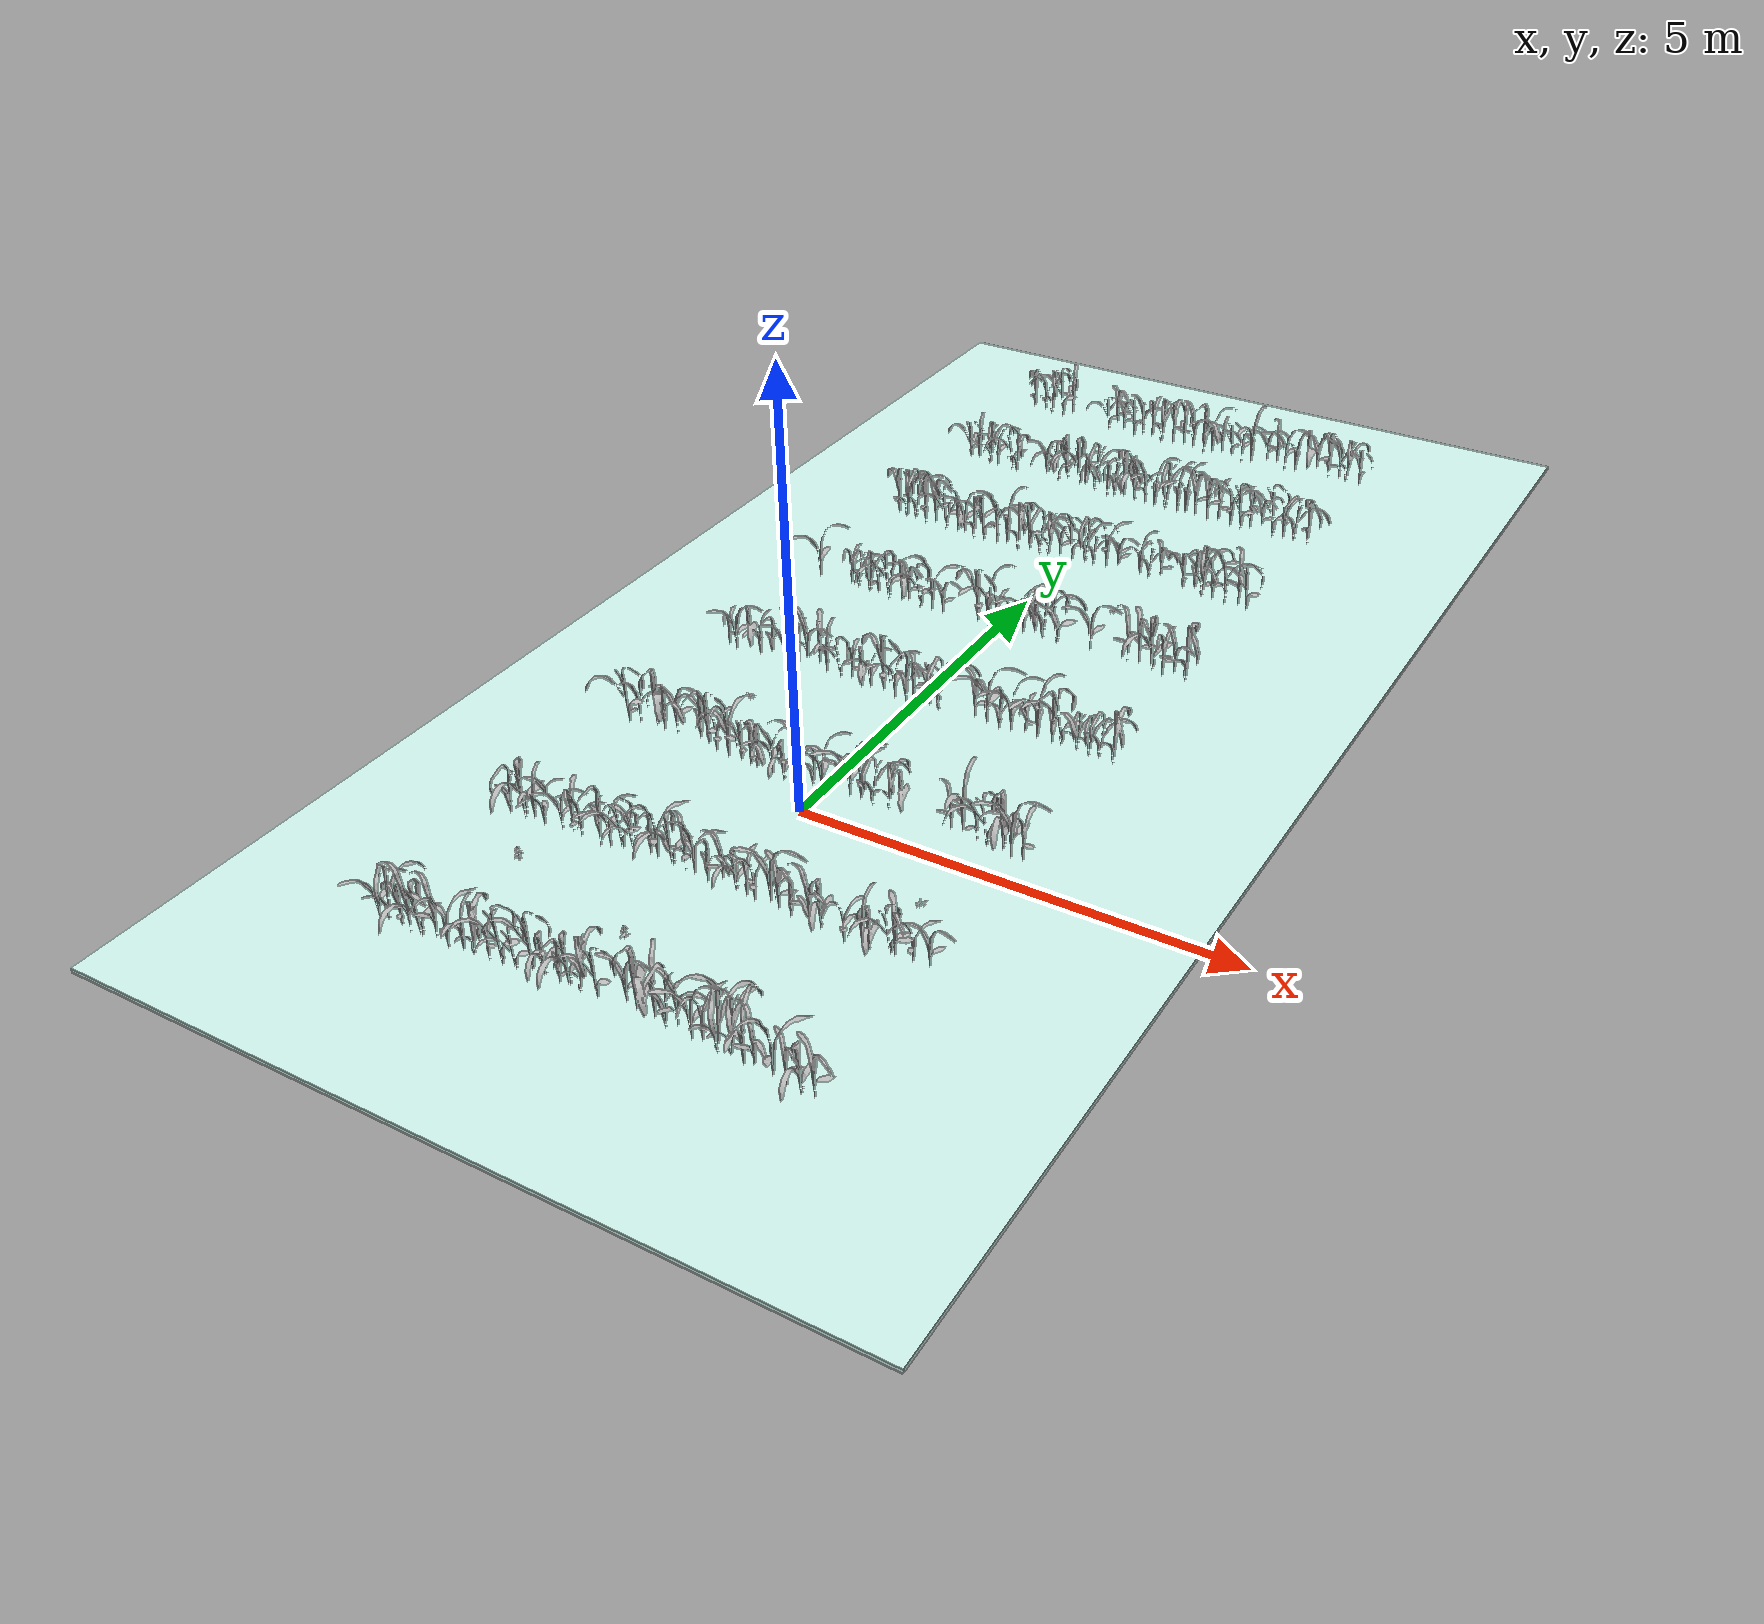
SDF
<sdf version="1.9">
 <world name="feild">
  <physics type="ode">
   <max_step_size>0.004</max_step_size>
   <real_time_factor>1.0</real_time_factor>
   <real_time_update_rate>250</real_time_update_rate>
  </physics>
  <plugin filename="gz-sim-physics-system" name="gz::sim::systems::Physics"/>
  <plugin filename="gz-sim-user-commands-system" name="gz::sim::systems::UserCommands"/>
  <plugin filename="gz-sim-scene-broadcaster-system" name="gz::sim::systems::SceneBroadcaster"/>
  <plugin filename="gz-sim-sensors-system" name="gz::sim::systems::Sensors">
   <render_engine>ogre2</render_engine>
  </plugin>
  <plugin filename="gz-sim-imu-system" name="gz::sim::systems::Imu"/>
  <plugin filename="gz-sim-navsat-system" name="gz::sim::systems::NavSat"/>
  <plugin filename="gz-sim-air-pressure-system" name="gz::sim::systems::AirPressure"/>
  <plugin filename="gz-sim-magnetometer-system" name="gz::sim::systems::Magnetometer"/>
  <scene>
   <grid>false</grid>
   <ambient>0.48 0.48 0.48 1</ambient>
   <background>0.7 0.8 1.0 1</background>
   <sky><clouds><speed>12</speed></clouds></sky>
  </scene>
  <light type="directional" name="sun">
   <pose>0 0 10 0 0 0</pose>
   <diffuse>0.87 0.87 0.87 1</diffuse>
   <specular>0.2 0.2 0.2 1</specular>
   <attenuation>
    <range>1000</range>
    <constant>0.9</constant>
    <linear>0.01</linear>
    <quadratic>0.001</quadratic>
   </attenuation>
   <direction>0.188 0.443 -0.877</direction>
  </light>
  <gravity>0 0 -9.8</gravity>
  <magnetic_field>6e-06 2.3e-05 -4.2e-05</magnetic_field>
  <atmosphere type="adiabatic"/>
  <model name="ground">
   <static>true</static>
   <pose>0.00 3.25 -0.025 0 0 0</pose>
   <link name="link">
    <collision name="collision">
     <geometry><box><size>9.00 17.30 0.05</size></box></geometry>
     <surface><friction><ode><mu>1.0</mu><mu2>1.0</mu2></ode></friction></surface>
    </collision>
    <visual name="visual">
     <geometry><box><size>9.00 17.30 0.05</size></box></geometry>
     <material>
      <diffuse>0.81 0.95 0.92 1</diffuse>
      <pbr>
       <metal>
        <albedo_map>model://materials/textures/grass_color.jpg</albedo_map>
        <normal_map>model://materials/textures/grass_normal.jpg</normal_map>
       </metal>
      </pbr>
     </material>
    </visual>
   </link>
  </model>
  <model name="row_01">
   <static>true</static>
   <pose>0 -3.400 0 0 0 0</pose>
   <link name="link">
    <visual name="p000">
     <pose>-2.470 -0.082 0.046 0 0 5.97</pose>
     <geometry>
      <mesh><uri>model://maize_02/meshes/maize_02.dae</uri><scale>0.6337 0.6337 0.6337</scale></mesh>
     </geometry>
    </visual>
    <collision name="p000_c">
     <pose>-2.470 -0.082 0.232 0 0 0</pose>
     <geometry><box><size>0.019 0.019 0.371</size></box></geometry>
    </collision>
    <visual name="p001">
     <pose>-2.368 -0.057 0.054 0 0 2.07</pose>
     <geometry>
      <mesh><uri>model://maize_01/meshes/maize_01.dae</uri><scale>0.7327 0.7327 0.7327</scale></mesh>
     </geometry>
    </visual>
    <collision name="p001_c">
     <pose>-2.368 -0.057 0.268 0 0 0</pose>
     <geometry><box><size>0.021 0.021 0.429</size></box></geometry>
    </collision>
    <visual name="p002">
     <pose>-2.182 -0.072 0.042 0 0 3.60</pose>
     <geometry>
      <mesh><uri>model://maize_01/meshes/maize_01.dae</uri><scale>0.5688 0.5688 0.5688</scale></mesh>
     </geometry>
    </visual>
    <collision name="p002_c">
     <pose>-2.182 -0.072 0.208 0 0 0</pose>
     <geometry><box><size>0.017 0.017 0.333</size></box></geometry>
    </collision>
    <visual name="p003">
     <pose>-2.075 -0.088 0.055 0 0 1.92</pose>
     <geometry>
      <mesh><uri>model://maize_02/meshes/maize_02.dae</uri><scale>0.7554 0.7554 0.7554</scale></mesh>
     </geometry>
    </visual>
    <collision name="p003_c">
     <pose>-2.075 -0.088 0.276 0 0 0</pose>
     <geometry><box><size>0.022 0.022 0.442</size></box></geometry>
    </collision>
    <visual name="p004">
     <pose>-1.923 -0.102 0.054 0 0 5.40</pose>
     <geometry>
      <mesh><uri>model://maize_01/meshes/maize_01.dae</uri><scale>0.7394 0.7394 0.7394</scale></mesh>
     </geometry>
    </visual>
    <collision name="p004_c">
     <pose>-1.923 -0.102 0.271 0 0 0</pose>
     <geometry><box><size>0.022 0.022 0.433</size></box></geometry>
    </collision>
    <visual name="p005">
     <pose>-1.777 -0.053 0.052 0 0 1.76</pose>
     <geometry>
      <mesh><uri>model://maize_02/meshes/maize_02.dae</uri><scale>0.7153 0.7153 0.7153</scale></mesh>
     </geometry>
    </visual>
    <collision name="p005_c">
     <pose>-1.777 -0.053 0.262 0 0 0</pose>
     <geometry><box><size>0.021 0.021 0.419</size></box></geometry>
    </collision>
    <visual name="p006">
     <pose>-1.603 -0.086 0.053 0 0 3.49</pose>
     <geometry>
      <mesh><uri>model://maize_02/meshes/maize_02.dae</uri><scale>0.7211 0.7211 0.7211</scale></mesh>
     </geometry>
    </visual>
    <collision name="p006_c">
     <pose>-1.603 -0.086 0.264 0 0 0</pose>
     <geometry><box><size>0.021 0.021 0.422</size></box></geometry>
    </collision>
    <visual name="p007">
     <pose>-1.456 -0.044 0.042 0 0 0.79</pose>
     <geometry>
      <mesh><uri>model://maize_02/meshes/maize_02.dae</uri><scale>0.5796 0.5796 0.5796</scale></mesh>
     </geometry>
    </visual>
    <collision name="p007_c">
     <pose>-1.456 -0.044 0.212 0 0 0</pose>
     <geometry><box><size>0.017 0.017 0.339</size></box></geometry>
    </collision>
    <visual name="p008">
     <pose>-1.323 -0.041 0.050 0 0 2.74</pose>
     <geometry>
      <mesh><uri>model://maize_01/meshes/maize_01.dae</uri><scale>0.6885 0.6885 0.6885</scale></mesh>
     </geometry>
    </visual>
    <collision name="p008_c">
     <pose>-1.323 -0.041 0.252 0 0 0</pose>
     <geometry><box><size>0.020 0.020 0.403</size></box></geometry>
    </collision>
    <visual name="p009">
     <pose>-1.173 -0.012 0.040 0 0 4.09</pose>
     <geometry>
      <mesh><uri>model://maize_02/meshes/maize_02.dae</uri><scale>0.5471 0.5471 0.5471</scale></mesh>
     </geometry>
    </visual>
    <collision name="p009_c">
     <pose>-1.173 -0.012 0.200 0 0 0</pose>
     <geometry><box><size>0.016 0.016 0.320</size></box></geometry>
    </collision>
    <visual name="p010">
     <pose>-1.006 -0.023 0.055 0 0 4.56</pose>
     <geometry>
      <mesh><uri>model://maize_01/meshes/maize_01.dae</uri><scale>0.7533 0.7533 0.7533</scale></mesh>
     </geometry>
    </visual>
    <collision name="p010_c">
     <pose>-1.006 -0.023 0.276 0 0 0</pose>
     <geometry><box><size>0.022 0.022 0.441</size></box></geometry>
    </collision>
    <visual name="p011">
     <pose>-0.853 -0.015 0.041 0 0 4.69</pose>
     <geometry>
      <mesh><uri>model://maize_01/meshes/maize_01.dae</uri><scale>0.5665 0.5665 0.5665</scale></mesh>
     </geometry>
    </visual>
    <collision name="p011_c">
     <pose>-0.853 -0.015 0.207 0 0 0</pose>
     <geometry><box><size>0.017 0.017 0.332</size></box></geometry>
    </collision>
    <visual name="p012">
     <pose>-0.691 0.038 0.056 0 0 4.17</pose>
     <geometry>
      <mesh><uri>model://maize_01/meshes/maize_01.dae</uri><scale>0.7600 0.7600 0.7600</scale></mesh>
     </geometry>
    </visual>
    <collision name="p012_c">
     <pose>-0.691 0.038 0.278 0 0 0</pose>
     <geometry><box><size>0.022 0.022 0.445</size></box></geometry>
    </collision>
    <visual name="p013">
     <pose>-0.549 0.036 0.043 0 0 5.82</pose>
     <geometry>
      <mesh><uri>model://maize_01/meshes/maize_01.dae</uri><scale>0.5893 0.5893 0.5893</scale></mesh>
     </geometry>
    </visual>
    <collision name="p013_c">
     <pose>-0.549 0.036 0.216 0 0 0</pose>
     <geometry><box><size>0.017 0.017 0.345</size></box></geometry>
    </collision>
    <visual name="p014">
     <pose>-0.378 0.034 0.042 0 0 0.62</pose>
     <geometry>
      <mesh><uri>model://maize_01/meshes/maize_01.dae</uri><scale>0.5764 0.5764 0.5764</scale></mesh>
     </geometry>
    </visual>
    <collision name="p014_c">
     <pose>-0.378 0.034 0.211 0 0 0</pose>
     <geometry><box><size>0.017 0.017 0.337</size></box></geometry>
    </collision>
    <visual name="p015">
     <pose>-0.266 0.036 0.051 0 0 5.57</pose>
     <geometry>
      <mesh><uri>model://maize_01/meshes/maize_01.dae</uri><scale>0.6982 0.6982 0.6982</scale></mesh>
     </geometry>
    </visual>
    <collision name="p015_c">
     <pose>-0.266 0.036 0.256 0 0 0</pose>
     <geometry><box><size>0.020 0.020 0.409</size></box></geometry>
    </collision>
    <visual name="p016">
     <pose>-0.130 0.039 0.053 0 0 2.55</pose>
     <geometry>
      <mesh><uri>model://maize_01/meshes/maize_01.dae</uri><scale>0.7198 0.7198 0.7198</scale></mesh>
     </geometry>
    </visual>
    <collision name="p016_c">
     <pose>-0.130 0.039 0.263 0 0 0</pose>
     <geometry><box><size>0.021 0.021 0.421</size></box></geometry>
    </collision>
    <visual name="p017">
     <pose>0.038 0.058 0.046 0 0 4.25</pose>
     <geometry>
      <mesh><uri>model://maize_01/meshes/maize_01.dae</uri><scale>0.6280 0.6280 0.6280</scale></mesh>
     </geometry>
    </visual>
    <collision name="p017_c">
     <pose>0.038 0.058 0.230 0 0 0</pose>
     <geometry><box><size>0.018 0.018 0.368</size></box></geometry>
    </collision>
    <visual name="p019">
     <pose>0.342 0.102 0.048 0 0 5.26</pose>
     <geometry>
      <mesh><uri>model://maize_02/meshes/maize_02.dae</uri><scale>0.6547 0.6547 0.6547</scale></mesh>
     </geometry>
    </visual>
    <collision name="p019_c">
     <pose>0.342 0.102 0.240 0 0 0</pose>
     <geometry><box><size>0.019 0.019 0.383</size></box></geometry>
    </collision>
    <visual name="p020">
     <pose>0.474 0.071 0.059 0 0 0.06</pose>
     <geometry>
      <mesh><uri>model://maize_01/meshes/maize_01.dae</uri><scale>0.8100 0.8100 0.8100</scale></mesh>
     </geometry>
    </visual>
    <collision name="p020_c">
     <pose>0.474 0.071 0.296 0 0 0</pose>
     <geometry><box><size>0.024 0.024 0.474</size></box></geometry>
    </collision>
    <visual name="p021">
     <pose>0.653 0.097 0.054 0 0 1.12</pose>
     <geometry>
      <mesh><uri>model://maize_02/meshes/maize_02.dae</uri><scale>0.7419 0.7419 0.7419</scale></mesh>
     </geometry>
    </visual>
    <collision name="p021_c">
     <pose>0.653 0.097 0.271 0 0 0</pose>
     <geometry><box><size>0.022 0.022 0.434</size></box></geometry>
    </collision>
    <visual name="p022">
     <pose>0.828 0.031 0.060 0 0 1.33</pose>
     <geometry>
      <mesh><uri>model://maize_01/meshes/maize_01.dae</uri><scale>0.8156 0.8156 0.8156</scale></mesh>
     </geometry>
    </visual>
    <collision name="p022_c">
     <pose>0.828 0.031 0.298 0 0 0</pose>
     <geometry><box><size>0.024 0.024 0.478</size></box></geometry>
    </collision>
    <visual name="p023">
     <pose>0.944 0.060 0.052 0 0 2.26</pose>
     <geometry>
      <mesh><uri>model://maize_02/meshes/maize_02.dae</uri><scale>0.7056 0.7056 0.7056</scale></mesh>
     </geometry>
    </visual>
    <collision name="p023_c">
     <pose>0.944 0.060 0.258 0 0 0</pose>
     <geometry><box><size>0.021 0.021 0.413</size></box></geometry>
    </collision>
    <visual name="p024">
     <pose>1.119 0.019 0.052 0 0 5.65</pose>
     <geometry>
      <mesh><uri>model://maize_02/meshes/maize_02.dae</uri><scale>0.7167 0.7167 0.7167</scale></mesh>
     </geometry>
    </visual>
    <collision name="p024_c">
     <pose>1.119 0.019 0.262 0 0 0</pose>
     <geometry><box><size>0.021 0.021 0.420</size></box></geometry>
    </collision>
    <visual name="p025">
     <pose>1.220 0.049 0.049 0 0 3.66</pose>
     <geometry>
      <mesh><uri>model://maize_02/meshes/maize_02.dae</uri><scale>0.6719 0.6719 0.6719</scale></mesh>
     </geometry>
    </visual>
    <collision name="p025_c">
     <pose>1.220 0.049 0.246 0 0 0</pose>
     <geometry><box><size>0.020 0.020 0.393</size></box></geometry>
    </collision>
    <visual name="p026">
     <pose>1.416 0.002 0.060 0 0 2.12</pose>
     <geometry>
      <mesh><uri>model://maize_01/meshes/maize_01.dae</uri><scale>0.8171 0.8171 0.8171</scale></mesh>
     </geometry>
    </visual>
    <collision name="p026_c">
     <pose>1.416 0.002 0.299 0 0 0</pose>
     <geometry><box><size>0.024 0.024 0.478</size></box></geometry>
    </collision>
    <visual name="p027">
     <pose>1.541 0.031 0.055 0 0 2.31</pose>
     <geometry>
      <mesh><uri>model://maize_01/meshes/maize_01.dae</uri><scale>0.7511 0.7511 0.7511</scale></mesh>
     </geometry>
    </visual>
    <collision name="p027_c">
     <pose>1.541 0.031 0.275 0 0 0</pose>
     <geometry><box><size>0.022 0.022 0.440</size></box></geometry>
    </collision>
    <visual name="p028">
     <pose>1.703 -0.026 0.055 0 0 0.88</pose>
     <geometry>
      <mesh><uri>model://maize_02/meshes/maize_02.dae</uri><scale>0.7456 0.7456 0.7456</scale></mesh>
     </geometry>
    </visual>
    <collision name="p028_c">
     <pose>1.703 -0.026 0.273 0 0 0</pose>
     <geometry><box><size>0.022 0.022 0.437</size></box></geometry>
    </collision>
    <visual name="p029">
     <pose>1.829 -0.042 0.051 0 0 1.55</pose>
     <geometry>
      <mesh><uri>model://maize_02/meshes/maize_02.dae</uri><scale>0.6904 0.6904 0.6904</scale></mesh>
     </geometry>
    </visual>
    <collision name="p029_c">
     <pose>1.829 -0.042 0.253 0 0 0</pose>
     <geometry><box><size>0.020 0.020 0.404</size></box></geometry>
    </collision>
    <visual name="p030">
     <pose>2.011 -0.021 0.058 0 0 3.18</pose>
     <geometry>
      <mesh><uri>model://maize_02/meshes/maize_02.dae</uri><scale>0.7949 0.7949 0.7949</scale></mesh>
     </geometry>
    </visual>
    <collision name="p030_c">
     <pose>2.011 -0.021 0.291 0 0 0</pose>
     <geometry><box><size>0.023 0.023 0.465</size></box></geometry>
    </collision>
    <visual name="p031">
     <pose>2.166 -0.044 0.045 0 0 4.64</pose>
     <geometry>
      <mesh><uri>model://maize_02/meshes/maize_02.dae</uri><scale>0.6199 0.6199 0.6199</scale></mesh>
     </geometry>
    </visual>
    <collision name="p031_c">
     <pose>2.166 -0.044 0.227 0 0 0</pose>
     <geometry><box><size>0.018 0.018 0.363</size></box></geometry>
    </collision>
    <visual name="p032">
     <pose>2.321 -0.064 0.047 0 0 5.68</pose>
     <geometry>
      <mesh><uri>model://maize_01/meshes/maize_01.dae</uri><scale>0.6431 0.6431 0.6431</scale></mesh>
     </geometry>
    </visual>
    <collision name="p032_c">
     <pose>2.321 -0.064 0.235 0 0 0</pose>
     <geometry><box><size>0.019 0.019 0.377</size></box></geometry>
    </collision>
    <visual name="p033">
     <pose>2.462 -0.058 0.051 0 0 4.73</pose>
     <geometry>
      <mesh><uri>model://maize_02/meshes/maize_02.dae</uri><scale>0.6938 0.6938 0.6938</scale></mesh>
     </geometry>
    </visual>
    <collision name="p033_c">
     <pose>2.462 -0.058 0.254 0 0 0</pose>
     <geometry><box><size>0.020 0.020 0.406</size></box></geometry>
    </collision>
   </link>
  </model>
  <model name="row_02">
   <static>true</static>
   <pose>0 -1.500 0 0 0 0</pose>
   <link name="link">
    <visual name="p000">
     <pose>-2.500 -0.068 0.049 0 0 1.13</pose>
     <geometry>
      <mesh><uri>model://maize_01/meshes/maize_01.dae</uri><scale>0.6752 0.6752 0.6752</scale></mesh>
     </geometry>
    </visual>
    <collision name="p000_c">
     <pose>-2.500 -0.068 0.247 0 0 0</pose>
     <geometry><box><size>0.020 0.020 0.395</size></box></geometry>
    </collision>
    <visual name="p001">
     <pose>-2.327 -0.044 0.058 0 0 5.54</pose>
     <geometry>
      <mesh><uri>model://maize_01/meshes/maize_01.dae</uri><scale>0.7953 0.7953 0.7953</scale></mesh>
     </geometry>
    </visual>
    <collision name="p001_c">
     <pose>-2.327 -0.044 0.291 0 0 0</pose>
     <geometry><box><size>0.023 0.023 0.466</size></box></geometry>
    </collision>
    <visual name="p002">
     <pose>-2.215 -0.024 0.046 0 0 0.92</pose>
     <geometry>
      <mesh><uri>model://maize_02/meshes/maize_02.dae</uri><scale>0.6334 0.6334 0.6334</scale></mesh>
     </geometry>
    </visual>
    <collision name="p002_c">
     <pose>-2.215 -0.024 0.232 0 0 0</pose>
     <geometry><box><size>0.019 0.019 0.371</size></box></geometry>
    </collision>
    <visual name="p003">
     <pose>-2.062 -0.055 0.041 0 0 0.28</pose>
     <geometry>
      <mesh><uri>model://maize_02/meshes/maize_02.dae</uri><scale>0.5573 0.5573 0.5573</scale></mesh>
     </geometry>
    </visual>
    <collision name="p003_c">
     <pose>-2.062 -0.055 0.204 0 0 0</pose>
     <geometry><box><size>0.016 0.016 0.326</size></box></geometry>
    </collision>
    <visual name="p004">
     <pose>-1.878 -0.001 0.042 0 0 5.67</pose>
     <geometry>
      <mesh><uri>model://maize_02/meshes/maize_02.dae</uri><scale>0.5726 0.5726 0.5726</scale></mesh>
     </geometry>
    </visual>
    <collision name="p004_c">
     <pose>-1.878 -0.001 0.210 0 0 0</pose>
     <geometry><box><size>0.017 0.017 0.335</size></box></geometry>
    </collision>
    <visual name="p005">
     <pose>-1.755 0.023 0.049 0 0 4.31</pose>
     <geometry>
      <mesh><uri>model://maize_02/meshes/maize_02.dae</uri><scale>0.6710 0.6710 0.6710</scale></mesh>
     </geometry>
    </visual>
    <collision name="p005_c">
     <pose>-1.755 0.023 0.246 0 0 0</pose>
     <geometry><box><size>0.020 0.020 0.393</size></box></geometry>
    </collision>
    <visual name="p006">
     <pose>-1.619 -0.011 0.042 0 0 2.80</pose>
     <geometry>
      <mesh><uri>model://maize_02/meshes/maize_02.dae</uri><scale>0.5787 0.5787 0.5787</scale></mesh>
     </geometry>
    </visual>
    <collision name="p006_c">
     <pose>-1.619 -0.011 0.212 0 0 0</pose>
     <geometry><box><size>0.017 0.017 0.339</size></box></geometry>
    </collision>
    <visual name="p007">
     <pose>-1.434 0.039 0.053 0 0 0.72</pose>
     <geometry>
      <mesh><uri>model://maize_01/meshes/maize_01.dae</uri><scale>0.7204 0.7204 0.7204</scale></mesh>
     </geometry>
    </visual>
    <collision name="p007_c">
     <pose>-1.434 0.039 0.264 0 0 0</pose>
     <geometry><box><size>0.021 0.021 0.422</size></box></geometry>
    </collision>
    <visual name="p008">
     <pose>-1.280 0.017 0.046 0 0 6.21</pose>
     <geometry>
      <mesh><uri>model://maize_02/meshes/maize_02.dae</uri><scale>0.6300 0.6300 0.6300</scale></mesh>
     </geometry>
    </visual>
    <collision name="p008_c">
     <pose>-1.280 0.017 0.231 0 0 0</pose>
     <geometry><box><size>0.018 0.018 0.369</size></box></geometry>
    </collision>
    <visual name="p009">
     <pose>-1.129 0.020 0.050 0 0 4.70</pose>
     <geometry>
      <mesh><uri>model://maize_01/meshes/maize_01.dae</uri><scale>0.6882 0.6882 0.6882</scale></mesh>
     </geometry>
    </visual>
    <collision name="p009_c">
     <pose>-1.129 0.020 0.252 0 0 0</pose>
     <geometry><box><size>0.020 0.020 0.403</size></box></geometry>
    </collision>
    <visual name="p010">
     <pose>-1.008 0.039 0.040 0 0 5.04</pose>
     <geometry>
      <mesh><uri>model://maize_01/meshes/maize_01.dae</uri><scale>0.5495 0.5495 0.5495</scale></mesh>
     </geometry>
    </visual>
    <collision name="p010_c">
     <pose>-1.008 0.039 0.201 0 0 0</pose>
     <geometry><box><size>0.016 0.016 0.322</size></box></geometry>
    </collision>
    <visual name="p011">
     <pose>-0.825 0.081 0.043 0 0 0.42</pose>
     <geometry>
      <mesh><uri>model://maize_01/meshes/maize_01.dae</uri><scale>0.5817 0.5817 0.5817</scale></mesh>
     </geometry>
    </visual>
    <collision name="p011_c">
     <pose>-0.825 0.081 0.213 0 0 0</pose>
     <geometry><box><size>0.017 0.017 0.341</size></box></geometry>
    </collision>
    <visual name="p012">
     <pose>-0.713 0.057 0.058 0 0 3.35</pose>
     <geometry>
      <mesh><uri>model://maize_02/meshes/maize_02.dae</uri><scale>0.7947 0.7947 0.7947</scale></mesh>
     </geometry>
    </visual>
    <collision name="p012_c">
     <pose>-0.713 0.057 0.291 0 0 0</pose>
     <geometry><box><size>0.023 0.023 0.465</size></box></geometry>
    </collision>
    <visual name="p013">
     <pose>-0.524 0.036 0.054 0 0 5.22</pose>
     <geometry>
      <mesh><uri>model://maize_01/meshes/maize_01.dae</uri><scale>0.7334 0.7334 0.7334</scale></mesh>
     </geometry>
    </visual>
    <collision name="p013_c">
     <pose>-0.524 0.036 0.268 0 0 0</pose>
     <geometry><box><size>0.021 0.021 0.429</size></box></geometry>
    </collision>
    <visual name="p014">
     <pose>-0.394 0.076 0.046 0 0 1.53</pose>
     <geometry>
      <mesh><uri>model://maize_02/meshes/maize_02.dae</uri><scale>0.6281 0.6281 0.6281</scale></mesh>
     </geometry>
    </visual>
    <collision name="p014_c">
     <pose>-0.394 0.076 0.230 0 0 0</pose>
     <geometry><box><size>0.018 0.018 0.368</size></box></geometry>
    </collision>
    <visual name="p015">
     <pose>-0.273 0.061 0.051 0 0 2.80</pose>
     <geometry>
      <mesh><uri>model://maize_02/meshes/maize_02.dae</uri><scale>0.6930 0.6930 0.6930</scale></mesh>
     </geometry>
    </visual>
    <collision name="p015_c">
     <pose>-0.273 0.061 0.254 0 0 0</pose>
     <geometry><box><size>0.020 0.020 0.406</size></box></geometry>
    </collision>
    <visual name="p016">
     <pose>-0.097 0.031 0.041 0 0 0.56</pose>
     <geometry>
      <mesh><uri>model://maize_01/meshes/maize_01.dae</uri><scale>0.5618 0.5618 0.5618</scale></mesh>
     </geometry>
    </visual>
    <collision name="p016_c">
     <pose>-0.097 0.031 0.206 0 0 0</pose>
     <geometry><box><size>0.016 0.016 0.329</size></box></geometry>
    </collision>
    <visual name="p017">
     <pose>0.074 0.057 0.045 0 0 1.93</pose>
     <geometry>
      <mesh><uri>model://maize_02/meshes/maize_02.dae</uri><scale>0.6184 0.6184 0.6184</scale></mesh>
     </geometry>
    </visual>
    <collision name="p017_c">
     <pose>0.074 0.057 0.226 0 0 0</pose>
     <geometry><box><size>0.018 0.018 0.362</size></box></geometry>
    </collision>
    <visual name="p018">
     <pose>0.224 0.056 0.041 0 0 5.44</pose>
     <geometry>
      <mesh><uri>model://maize_01/meshes/maize_01.dae</uri><scale>0.5638 0.5638 0.5638</scale></mesh>
     </geometry>
    </visual>
    <collision name="p018_c">
     <pose>0.224 0.056 0.206 0 0 0</pose>
     <geometry><box><size>0.017 0.017 0.330</size></box></geometry>
    </collision>
    <visual name="p019">
     <pose>0.364 0.040 0.043 0 0 4.02</pose>
     <geometry>
      <mesh><uri>model://maize_02/meshes/maize_02.dae</uri><scale>0.5896 0.5896 0.5896</scale></mesh>
     </geometry>
    </visual>
    <collision name="p019_c">
     <pose>0.364 0.040 0.216 0 0 0</pose>
     <geometry><box><size>0.017 0.017 0.345</size></box></geometry>
    </collision>
    <visual name="p020">
     <pose>0.473 0.017 0.044 0 0 3.39</pose>
     <geometry>
      <mesh><uri>model://maize_02/meshes/maize_02.dae</uri><scale>0.6060 0.6060 0.6060</scale></mesh>
     </geometry>
    </visual>
    <collision name="p020_c">
     <pose>0.473 0.017 0.222 0 0 0</pose>
     <geometry><box><size>0.018 0.018 0.355</size></box></geometry>
    </collision>
    <visual name="p021">
     <pose>0.666 0.015 0.058 0 0 5.39</pose>
     <geometry>
      <mesh><uri>model://maize_02/meshes/maize_02.dae</uri><scale>0.7913 0.7913 0.7913</scale></mesh>
     </geometry>
    </visual>
    <collision name="p021_c">
     <pose>0.666 0.015 0.290 0 0 0</pose>
     <geometry><box><size>0.023 0.023 0.463</size></box></geometry>
    </collision>
    <visual name="p022">
     <pose>0.797 -0.038 0.053 0 0 4.67</pose>
     <geometry>
      <mesh><uri>model://maize_02/meshes/maize_02.dae</uri><scale>0.7201 0.7201 0.7201</scale></mesh>
     </geometry>
    </visual>
    <collision name="p022_c">
     <pose>0.797 -0.038 0.264 0 0 0</pose>
     <geometry><box><size>0.021 0.021 0.422</size></box></geometry>
    </collision>
    <visual name="p023">
     <pose>0.932 -0.045 0.040 0 0 0.33</pose>
     <geometry>
      <mesh><uri>model://maize_01/meshes/maize_01.dae</uri><scale>0.5467 0.5467 0.5467</scale></mesh>
     </geometry>
    </visual>
    <collision name="p023_c">
     <pose>0.932 -0.045 0.200 0 0 0</pose>
     <geometry><box><size>0.016 0.016 0.320</size></box></geometry>
    </collision>
    <visual name="p024">
     <pose>1.129 -0.034 0.048 0 0 1.74</pose>
     <geometry>
      <mesh><uri>model://maize_02/meshes/maize_02.dae</uri><scale>0.6499 0.6499 0.6499</scale></mesh>
     </geometry>
    </visual>
    <collision name="p024_c">
     <pose>1.129 -0.034 0.238 0 0 0</pose>
     <geometry><box><size>0.019 0.019 0.381</size></box></geometry>
    </collision>
    <visual name="p025">
     <pose>1.256 -0.023 0.046 0 0 5.88</pose>
     <geometry>
      <mesh><uri>model://maize_01/meshes/maize_01.dae</uri><scale>0.6336 0.6336 0.6336</scale></mesh>
     </geometry>
    </visual>
    <collision name="p025_c">
     <pose>1.256 -0.023 0.232 0 0 0</pose>
     <geometry><box><size>0.019 0.019 0.371</size></box></geometry>
    </collision>
    <visual name="p027">
     <pose>1.552 -0.080 0.043 0 0 3.44</pose>
     <geometry>
      <mesh><uri>model://maize_02/meshes/maize_02.dae</uri><scale>0.5870 0.5870 0.5870</scale></mesh>
     </geometry>
    </visual>
    <collision name="p027_c">
     <pose>1.552 -0.080 0.215 0 0 0</pose>
     <geometry><box><size>0.017 0.017 0.344</size></box></geometry>
    </collision>
    <visual name="p028">
     <pose>1.723 -0.033 0.046 0 0 0.63</pose>
     <geometry>
      <mesh><uri>model://maize_02/meshes/maize_02.dae</uri><scale>0.6262 0.6262 0.6262</scale></mesh>
     </geometry>
    </visual>
    <collision name="p028_c">
     <pose>1.723 -0.033 0.229 0 0 0</pose>
     <geometry><box><size>0.018 0.018 0.367</size></box></geometry>
    </collision>
    <visual name="p029">
     <pose>1.832 -0.087 0.043 0 0 5.97</pose>
     <geometry>
      <mesh><uri>model://maize_01/meshes/maize_01.dae</uri><scale>0.5888 0.5888 0.5888</scale></mesh>
     </geometry>
    </visual>
    <collision name="p029_c">
     <pose>1.832 -0.087 0.215 0 0 0</pose>
     <geometry><box><size>0.017 0.017 0.345</size></box></geometry>
    </collision>
    <visual name="p030">
     <pose>2.027 -0.030 0.047 0 0 4.71</pose>
     <geometry>
      <mesh><uri>model://maize_01/meshes/maize_01.dae</uri><scale>0.6463 0.6463 0.6463</scale></mesh>
     </geometry>
    </visual>
    <collision name="p030_c">
     <pose>2.027 -0.030 0.236 0 0 0</pose>
     <geometry><box><size>0.019 0.019 0.378</size></box></geometry>
    </collision>
    <visual name="p031">
     <pose>2.122 -0.085 0.056 0 0 4.42</pose>
     <geometry>
      <mesh><uri>model://maize_02/meshes/maize_02.dae</uri><scale>0.7611 0.7611 0.7611</scale></mesh>
     </geometry>
    </visual>
    <collision name="p031_c">
     <pose>2.122 -0.085 0.279 0 0 0</pose>
     <geometry><box><size>0.022 0.022 0.446</size></box></geometry>
    </collision>
    <visual name="p032">
     <pose>2.273 -0.018 0.042 0 0 3.20</pose>
     <geometry>
      <mesh><uri>model://maize_02/meshes/maize_02.dae</uri><scale>0.5697 0.5697 0.5697</scale></mesh>
     </geometry>
    </visual>
    <collision name="p032_c">
     <pose>2.273 -0.018 0.208 0 0 0</pose>
     <geometry><box><size>0.017 0.017 0.334</size></box></geometry>
    </collision>
    <visual name="p033">
     <pose>2.448 -0.011 0.042 0 0 5.14</pose>
     <geometry>
      <mesh><uri>model://maize_02/meshes/maize_02.dae</uri><scale>0.5697 0.5697 0.5697</scale></mesh>
     </geometry>
    </visual>
    <collision name="p033_c">
     <pose>2.448 -0.011 0.208 0 0 0</pose>
     <geometry><box><size>0.017 0.017 0.334</size></box></geometry>
    </collision>
   </link>
  </model>
  <model name="row_03">
   <static>true</static>
   <pose>0 0.400 0 0 0 0</pose>
   <link name="link">
    <visual name="p000">
     <pose>-2.514 0.016 0.056 0 0 4.29</pose>
     <geometry>
      <mesh><uri>model://maize_01/meshes/maize_01.dae</uri><scale>0.7590 0.7590 0.7590</scale></mesh>
     </geometry>
    </visual>
    <collision name="p000_c">
     <pose>-2.514 0.016 0.278 0 0 0</pose>
     <geometry><box><size>0.022 0.022 0.444</size></box></geometry>
    </collision>
    <visual name="p001">
     <pose>-2.380 0.047 0.042 0 0 2.70</pose>
     <geometry>
      <mesh><uri>model://maize_02/meshes/maize_02.dae</uri><scale>0.5744 0.5744 0.5744</scale></mesh>
     </geometry>
    </visual>
    <collision name="p001_c">
     <pose>-2.380 0.047 0.210 0 0 0</pose>
     <geometry><box><size>0.017 0.017 0.336</size></box></geometry>
    </collision>
    <visual name="p002">
     <pose>-2.186 0.082 0.058 0 0 6.25</pose>
     <geometry>
      <mesh><uri>model://maize_01/meshes/maize_01.dae</uri><scale>0.7957 0.7957 0.7957</scale></mesh>
     </geometry>
    </visual>
    <collision name="p002_c">
     <pose>-2.186 0.082 0.291 0 0 0</pose>
     <geometry><box><size>0.023 0.023 0.466</size></box></geometry>
    </collision>
    <visual name="p003">
     <pose>-2.066 0.058 0.047 0 0 0.44</pose>
     <geometry>
      <mesh><uri>model://maize_01/meshes/maize_01.dae</uri><scale>0.6481 0.6481 0.6481</scale></mesh>
     </geometry>
    </visual>
    <collision name="p003_c">
     <pose>-2.066 0.058 0.237 0 0 0</pose>
     <geometry><box><size>0.019 0.019 0.379</size></box></geometry>
    </collision>
    <visual name="p004">
     <pose>-1.915 0.091 0.052 0 0 5.27</pose>
     <geometry>
      <mesh><uri>model://maize_02/meshes/maize_02.dae</uri><scale>0.7047 0.7047 0.7047</scale></mesh>
     </geometry>
    </visual>
    <collision name="p004_c">
     <pose>-1.915 0.091 0.258 0 0 0</pose>
     <geometry><box><size>0.021 0.021 0.413</size></box></geometry>
    </collision>
    <visual name="p006">
     <pose>-1.582 0.064 0.053 0 0 0.52</pose>
     <geometry>
      <mesh><uri>model://maize_01/meshes/maize_01.dae</uri><scale>0.7249 0.7249 0.7249</scale></mesh>
     </geometry>
    </visual>
    <collision name="p006_c">
     <pose>-1.582 0.064 0.265 0 0 0</pose>
     <geometry><box><size>0.021 0.021 0.424</size></box></geometry>
    </collision>
    <visual name="p007">
     <pose>-1.443 0.031 0.056 0 0 3.80</pose>
     <geometry>
      <mesh><uri>model://maize_01/meshes/maize_01.dae</uri><scale>0.7638 0.7638 0.7638</scale></mesh>
     </geometry>
    </visual>
    <collision name="p007_c">
     <pose>-1.443 0.031 0.280 0 0 0</pose>
     <geometry><box><size>0.022 0.022 0.447</size></box></geometry>
    </collision>
    <visual name="p008">
     <pose>-1.313 -0.012 0.047 0 0 3.64</pose>
     <geometry>
      <mesh><uri>model://maize_02/meshes/maize_02.dae</uri><scale>0.6411 0.6411 0.6411</scale></mesh>
     </geometry>
    </visual>
    <collision name="p008_c">
     <pose>-1.313 -0.012 0.235 0 0 0</pose>
     <geometry><box><size>0.019 0.019 0.375</size></box></geometry>
    </collision>
    <visual name="p009">
     <pose>-1.161 -0.012 0.058 0 0 3.81</pose>
     <geometry>
      <mesh><uri>model://maize_02/meshes/maize_02.dae</uri><scale>0.7976 0.7976 0.7976</scale></mesh>
     </geometry>
    </visual>
    <collision name="p009_c">
     <pose>-1.161 -0.012 0.292 0 0 0</pose>
     <geometry><box><size>0.023 0.023 0.467</size></box></geometry>
    </collision>
    <visual name="p010">
     <pose>-0.979 -0.020 0.043 0 0 3.66</pose>
     <geometry>
      <mesh><uri>model://maize_01/meshes/maize_01.dae</uri><scale>0.5868 0.5868 0.5868</scale></mesh>
     </geometry>
    </visual>
    <collision name="p010_c">
     <pose>-0.979 -0.020 0.215 0 0 0</pose>
     <geometry><box><size>0.017 0.017 0.344</size></box></geometry>
    </collision>
    <visual name="p011">
     <pose>-0.833 -0.069 0.044 0 0 0.21</pose>
     <geometry>
      <mesh><uri>model://maize_01/meshes/maize_01.dae</uri><scale>0.5956 0.5956 0.5956</scale></mesh>
     </geometry>
    </visual>
    <collision name="p011_c">
     <pose>-0.833 -0.069 0.218 0 0 0</pose>
     <geometry><box><size>0.017 0.017 0.349</size></box></geometry>
    </collision>
    <visual name="p012">
     <pose>-0.724 -0.086 0.049 0 0 3.24</pose>
     <geometry>
      <mesh><uri>model://maize_01/meshes/maize_01.dae</uri><scale>0.6717 0.6717 0.6717</scale></mesh>
     </geometry>
    </visual>
    <collision name="p012_c">
     <pose>-0.724 -0.086 0.246 0 0 0</pose>
     <geometry><box><size>0.020 0.020 0.393</size></box></geometry>
    </collision>
    <visual name="p013">
     <pose>-0.576 -0.043 0.046 0 0 6.15</pose>
     <geometry>
      <mesh><uri>model://maize_02/meshes/maize_02.dae</uri><scale>0.6242 0.6242 0.6242</scale></mesh>
     </geometry>
    </visual>
    <collision name="p013_c">
     <pose>-0.576 -0.043 0.228 0 0 0</pose>
     <geometry><box><size>0.018 0.018 0.366</size></box></geometry>
    </collision>
    <visual name="p014">
     <pose>-0.409 -0.078 0.041 0 0 5.66</pose>
     <geometry>
      <mesh><uri>model://maize_01/meshes/maize_01.dae</uri><scale>0.5643 0.5643 0.5643</scale></mesh>
     </geometry>
    </visual>
    <collision name="p014_c">
     <pose>-0.409 -0.078 0.206 0 0 0</pose>
     <geometry><box><size>0.017 0.017 0.330</size></box></geometry>
    </collision>
    <visual name="p015">
     <pose>-0.223 -0.067 0.057 0 0 2.05</pose>
     <geometry>
      <mesh><uri>model://maize_02/meshes/maize_02.dae</uri><scale>0.7739 0.7739 0.7739</scale></mesh>
     </geometry>
    </visual>
    <collision name="p015_c">
     <pose>-0.223 -0.067 0.283 0 0 0</pose>
     <geometry><box><size>0.023 0.023 0.453</size></box></geometry>
    </collision>
    <visual name="p016">
     <pose>-0.072 -0.027 0.041 0 0 0.91</pose>
     <geometry>
      <mesh><uri>model://maize_01/meshes/maize_01.dae</uri><scale>0.5534 0.5534 0.5534</scale></mesh>
     </geometry>
    </visual>
    <collision name="p016_c">
     <pose>-0.072 -0.027 0.203 0 0 0</pose>
     <geometry><box><size>0.016 0.016 0.324</size></box></geometry>
    </collision>
    <visual name="p017">
     <pose>0.065 -0.068 0.054 0 0 0.02</pose>
     <geometry>
      <mesh><uri>model://maize_02/meshes/maize_02.dae</uri><scale>0.7423 0.7423 0.7423</scale></mesh>
     </geometry>
    </visual>
    <collision name="p017_c">
     <pose>0.065 -0.068 0.272 0 0 0</pose>
     <geometry><box><size>0.022 0.022 0.435</size></box></geometry>
    </collision>
    <visual name="p019">
     <pose>0.379 -0.019 0.058 0 0 5.85</pose>
     <geometry>
      <mesh><uri>model://maize_02/meshes/maize_02.dae</uri><scale>0.7911 0.7911 0.7911</scale></mesh>
     </geometry>
    </visual>
    <collision name="p019_c">
     <pose>0.379 -0.019 0.289 0 0 0</pose>
     <geometry><box><size>0.023 0.023 0.463</size></box></geometry>
    </collision>
    <visual name="p020">
     <pose>0.503 0.002 0.053 0 0 3.51</pose>
     <geometry>
      <mesh><uri>model://maize_02/meshes/maize_02.dae</uri><scale>0.7218 0.7218 0.7218</scale></mesh>
     </geometry>
    </visual>
    <collision name="p020_c">
     <pose>0.503 0.002 0.264 0 0 0</pose>
     <geometry><box><size>0.021 0.021 0.423</size></box></geometry>
    </collision>
    <visual name="p021">
     <pose>0.633 0.021 0.048 0 0 1.59</pose>
     <geometry>
      <mesh><uri>model://maize_01/meshes/maize_01.dae</uri><scale>0.6605 0.6605 0.6605</scale></mesh>
     </geometry>
    </visual>
    <collision name="p021_c">
     <pose>0.633 0.021 0.242 0 0 0</pose>
     <geometry><box><size>0.019 0.019 0.387</size></box></geometry>
    </collision>
    <visual name="p022">
     <pose>0.812 0.047 0.047 0 0 2.33</pose>
     <geometry>
      <mesh><uri>model://maize_01/meshes/maize_01.dae</uri><scale>0.6360 0.6360 0.6360</scale></mesh>
     </geometry>
    </visual>
    <collision name="p022_c">
     <pose>0.812 0.047 0.233 0 0 0</pose>
     <geometry><box><size>0.019 0.019 0.372</size></box></geometry>
    </collision>
    <visual name="p023">
     <pose>0.948 0.053 0.041 0 0 6.05</pose>
     <geometry>
      <mesh><uri>model://maize_01/meshes/maize_01.dae</uri><scale>0.5668 0.5668 0.5668</scale></mesh>
     </geometry>
    </visual>
    <collision name="p023_c">
     <pose>0.948 0.053 0.207 0 0 0</pose>
     <geometry><box><size>0.017 0.017 0.332</size></box></geometry>
    </collision>
    <visual name="p027">
     <pose>1.556 0.025 0.042 0 0 1.51</pose>
     <geometry>
      <mesh><uri>model://maize_02/meshes/maize_02.dae</uri><scale>0.5714 0.5714 0.5714</scale></mesh>
     </geometry>
    </visual>
    <collision name="p027_c">
     <pose>1.556 0.025 0.209 0 0 0</pose>
     <geometry><box><size>0.017 0.017 0.335</size></box></geometry>
    </collision>
    <visual name="p028">
     <pose>1.678 0.053 0.059 0 0 0.69</pose>
     <geometry>
      <mesh><uri>model://maize_02/meshes/maize_02.dae</uri><scale>0.8059 0.8059 0.8059</scale></mesh>
     </geometry>
    </visual>
    <collision name="p028_c">
     <pose>1.678 0.053 0.295 0 0 0</pose>
     <geometry><box><size>0.024 0.024 0.472</size></box></geometry>
    </collision>
    <visual name="p029">
     <pose>1.873 -0.004 0.041 0 0 2.48</pose>
     <geometry>
      <mesh><uri>model://maize_02/meshes/maize_02.dae</uri><scale>0.5603 0.5603 0.5603</scale></mesh>
     </geometry>
    </visual>
    <collision name="p029_c">
     <pose>1.873 -0.004 0.205 0 0 0</pose>
     <geometry><box><size>0.016 0.016 0.328</size></box></geometry>
    </collision>
    <visual name="p030">
     <pose>1.995 -0.026 0.053 0 0 4.62</pose>
     <geometry>
      <mesh><uri>model://maize_01/meshes/maize_01.dae</uri><scale>0.7192 0.7192 0.7192</scale></mesh>
     </geometry>
    </visual>
    <collision name="p030_c">
     <pose>1.995 -0.026 0.263 0 0 0</pose>
     <geometry><box><size>0.021 0.021 0.421</size></box></geometry>
    </collision>
    <visual name="p031">
     <pose>2.173 -0.006 0.057 0 0 5.78</pose>
     <geometry>
      <mesh><uri>model://maize_01/meshes/maize_01.dae</uri><scale>0.7788 0.7788 0.7788</scale></mesh>
     </geometry>
    </visual>
    <collision name="p031_c">
     <pose>2.173 -0.006 0.285 0 0 0</pose>
     <geometry><box><size>0.023 0.023 0.456</size></box></geometry>
    </collision>
    <visual name="p032">
     <pose>2.300 -0.072 0.058 0 0 5.45</pose>
     <geometry>
      <mesh><uri>model://maize_02/meshes/maize_02.dae</uri><scale>0.7959 0.7959 0.7959</scale></mesh>
     </geometry>
    </visual>
    <collision name="p032_c">
     <pose>2.300 -0.072 0.291 0 0 0</pose>
     <geometry><box><size>0.023 0.023 0.466</size></box></geometry>
    </collision>
    <visual name="p033">
     <pose>2.434 -0.072 0.049 0 0 3.89</pose>
     <geometry>
      <mesh><uri>model://maize_02/meshes/maize_02.dae</uri><scale>0.6759 0.6759 0.6759</scale></mesh>
     </geometry>
    </visual>
    <collision name="p033_c">
     <pose>2.434 -0.072 0.247 0 0 0</pose>
     <geometry><box><size>0.020 0.020 0.396</size></box></geometry>
    </collision>
   </link>
  </model>
  <model name="row_04">
   <static>true</static>
   <pose>0 2.300 0 0 0 0</pose>
   <link name="link">
    <visual name="p000">
     <pose>-2.500 -0.004 0.040 0 0 4.12</pose>
     <geometry>
      <mesh><uri>model://maize_02/meshes/maize_02.dae</uri><scale>0.5503 0.5503 0.5503</scale></mesh>
     </geometry>
    </visual>
    <collision name="p000_c">
     <pose>-2.500 -0.004 0.201 0 0 0</pose>
     <geometry><box><size>0.016 0.016 0.322</size></box></geometry>
    </collision>
    <visual name="p001">
     <pose>-2.373 -0.047 0.049 0 0 5.62</pose>
     <geometry>
      <mesh><uri>model://maize_02/meshes/maize_02.dae</uri><scale>0.6664 0.6664 0.6664</scale></mesh>
     </geometry>
    </visual>
    <collision name="p001_c">
     <pose>-2.373 -0.047 0.244 0 0 0</pose>
     <geometry><box><size>0.020 0.020 0.390</size></box></geometry>
    </collision>
    <visual name="p002">
     <pose>-2.225 0.014 0.048 0 0 6.17</pose>
     <geometry>
      <mesh><uri>model://maize_01/meshes/maize_01.dae</uri><scale>0.6543 0.6543 0.6543</scale></mesh>
     </geometry>
    </visual>
    <collision name="p002_c">
     <pose>-2.225 0.014 0.239 0 0 0</pose>
     <geometry><box><size>0.019 0.019 0.383</size></box></geometry>
    </collision>
    <visual name="p003">
     <pose>-2.065 -0.009 0.041 0 0 0.52</pose>
     <geometry>
      <mesh><uri>model://maize_02/meshes/maize_02.dae</uri><scale>0.5653 0.5653 0.5653</scale></mesh>
     </geometry>
    </visual>
    <collision name="p003_c">
     <pose>-2.065 -0.009 0.207 0 0 0</pose>
     <geometry><box><size>0.017 0.017 0.331</size></box></geometry>
    </collision>
    <visual name="p004">
     <pose>-1.928 0.036 0.043 0 0 0.68</pose>
     <geometry>
      <mesh><uri>model://maize_01/meshes/maize_01.dae</uri><scale>0.5823 0.5823 0.5823</scale></mesh>
     </geometry>
    </visual>
    <collision name="p004_c">
     <pose>-1.928 0.036 0.213 0 0 0</pose>
     <geometry><box><size>0.017 0.017 0.341</size></box></geometry>
    </collision>
    <visual name="p005">
     <pose>-1.754 0.023 0.043 0 0 5.47</pose>
     <geometry>
      <mesh><uri>model://maize_02/meshes/maize_02.dae</uri><scale>0.5925 0.5925 0.5925</scale></mesh>
     </geometry>
    </visual>
    <collision name="p005_c">
     <pose>-1.754 0.023 0.217 0 0 0</pose>
     <geometry><box><size>0.017 0.017 0.347</size></box></geometry>
    </collision>
    <visual name="p006">
     <pose>-1.576 0.053 0.041 0 0 0.70</pose>
     <geometry>
      <mesh><uri>model://maize_02/meshes/maize_02.dae</uri><scale>0.5587 0.5587 0.5587</scale></mesh>
     </geometry>
    </visual>
    <collision name="p006_c">
     <pose>-1.576 0.053 0.204 0 0 0</pose>
     <geometry><box><size>0.016 0.016 0.327</size></box></geometry>
    </collision>
    <visual name="p007">
     <pose>-1.452 0.053 0.057 0 0 2.01</pose>
     <geometry>
      <mesh><uri>model://maize_02/meshes/maize_02.dae</uri><scale>0.7807 0.7807 0.7807</scale></mesh>
     </geometry>
    </visual>
    <collision name="p007_c">
     <pose>-1.452 0.053 0.286 0 0 0</pose>
     <geometry><box><size>0.023 0.023 0.457</size></box></geometry>
    </collision>
    <visual name="p008">
     <pose>-1.277 0.062 0.059 0 0 4.34</pose>
     <geometry>
      <mesh><uri>model://maize_02/meshes/maize_02.dae</uri><scale>0.8067 0.8067 0.8067</scale></mesh>
     </geometry>
    </visual>
    <collision name="p008_c">
     <pose>-1.277 0.062 0.295 0 0 0</pose>
     <geometry><box><size>0.024 0.024 0.472</size></box></geometry>
    </collision>
    <visual name="p009">
     <pose>-1.176 0.038 0.049 0 0 0.80</pose>
     <geometry>
      <mesh><uri>model://maize_02/meshes/maize_02.dae</uri><scale>0.6675 0.6675 0.6675</scale></mesh>
     </geometry>
    </visual>
    <collision name="p009_c">
     <pose>-1.176 0.038 0.244 0 0 0</pose>
     <geometry><box><size>0.020 0.020 0.391</size></box></geometry>
    </collision>
    <visual name="p010">
     <pose>-0.992 0.029 0.044 0 0 4.68</pose>
     <geometry>
      <mesh><uri>model://maize_01/meshes/maize_01.dae</uri><scale>0.5979 0.5979 0.5979</scale></mesh>
     </geometry>
    </visual>
    <collision name="p010_c">
     <pose>-0.992 0.029 0.219 0 0 0</pose>
     <geometry><box><size>0.018 0.018 0.350</size></box></geometry>
    </collision>
    <visual name="p011">
     <pose>-0.827 0.030 0.043 0 0 4.08</pose>
     <geometry>
      <mesh><uri>model://maize_02/meshes/maize_02.dae</uri><scale>0.5867 0.5867 0.5867</scale></mesh>
     </geometry>
    </visual>
    <collision name="p011_c">
     <pose>-0.827 0.030 0.215 0 0 0</pose>
     <geometry><box><size>0.017 0.017 0.344</size></box></geometry>
    </collision>
    <visual name="p012">
     <pose>-0.687 0.004 0.041 0 0 6.03</pose>
     <geometry>
      <mesh><uri>model://maize_01/meshes/maize_01.dae</uri><scale>0.5650 0.5650 0.5650</scale></mesh>
     </geometry>
    </visual>
    <collision name="p012_c">
     <pose>-0.687 0.004 0.207 0 0 0</pose>
     <geometry><box><size>0.017 0.017 0.331</size></box></geometry>
    </collision>
    <visual name="p013">
     <pose>-0.577 0.017 0.040 0 0 6.10</pose>
     <geometry>
      <mesh><uri>model://maize_02/meshes/maize_02.dae</uri><scale>0.5527 0.5527 0.5527</scale></mesh>
     </geometry>
    </visual>
    <collision name="p013_c">
     <pose>-0.577 0.017 0.202 0 0 0</pose>
     <geometry><box><size>0.016 0.016 0.324</size></box></geometry>
    </collision>
    <visual name="p014">
     <pose>-0.383 -0.001 0.060 0 0 3.39</pose>
     <geometry>
      <mesh><uri>model://maize_01/meshes/maize_01.dae</uri><scale>0.8183 0.8183 0.8183</scale></mesh>
     </geometry>
    </visual>
    <collision name="p014_c">
     <pose>-0.383 -0.001 0.299 0 0 0</pose>
     <geometry><box><size>0.024 0.024 0.479</size></box></geometry>
    </collision>
    <visual name="p015">
     <pose>-0.237 -0.013 0.046 0 0 6.10</pose>
     <geometry>
      <mesh><uri>model://maize_02/meshes/maize_02.dae</uri><scale>0.6328 0.6328 0.6328</scale></mesh>
     </geometry>
    </visual>
    <collision name="p015_c">
     <pose>-0.237 -0.013 0.232 0 0 0</pose>
     <geometry><box><size>0.019 0.019 0.370</size></box></geometry>
    </collision>
    <visual name="p016">
     <pose>-0.072 -0.048 0.052 0 0 0.67</pose>
     <geometry>
      <mesh><uri>model://maize_01/meshes/maize_01.dae</uri><scale>0.7115 0.7115 0.7115</scale></mesh>
     </geometry>
    </visual>
    <collision name="p016_c">
     <pose>-0.072 -0.048 0.260 0 0 0</pose>
     <geometry><box><size>0.021 0.021 0.417</size></box></geometry>
    </collision>
    <visual name="p017">
     <pose>0.029 -0.041 0.051 0 0 4.39</pose>
     <geometry>
      <mesh><uri>model://maize_02/meshes/maize_02.dae</uri><scale>0.7026 0.7026 0.7026</scale></mesh>
     </geometry>
    </visual>
    <collision name="p017_c">
     <pose>0.029 -0.041 0.257 0 0 0</pose>
     <geometry><box><size>0.021 0.021 0.411</size></box></geometry>
    </collision>
    <visual name="p018">
     <pose>0.217 -0.014 0.047 0 0 3.61</pose>
     <geometry>
      <mesh><uri>model://maize_01/meshes/maize_01.dae</uri><scale>0.6467 0.6467 0.6467</scale></mesh>
     </geometry>
    </visual>
    <collision name="p018_c">
     <pose>0.217 -0.014 0.237 0 0 0</pose>
     <geometry><box><size>0.019 0.019 0.379</size></box></geometry>
    </collision>
    <visual name="p019">
     <pose>0.340 -0.026 0.057 0 0 1.52</pose>
     <geometry>
      <mesh><uri>model://maize_01/meshes/maize_01.dae</uri><scale>0.7778 0.7778 0.7778</scale></mesh>
     </geometry>
    </visual>
    <collision name="p019_c">
     <pose>0.340 -0.026 0.285 0 0 0</pose>
     <geometry><box><size>0.023 0.023 0.455</size></box></geometry>
    </collision>
    <visual name="p022">
     <pose>0.790 -0.001 0.051 0 0 4.56</pose>
     <geometry>
      <mesh><uri>model://maize_02/meshes/maize_02.dae</uri><scale>0.7036 0.7036 0.7036</scale></mesh>
     </geometry>
    </visual>
    <collision name="p022_c">
     <pose>0.790 -0.001 0.257 0 0 0</pose>
     <geometry><box><size>0.021 0.021 0.412</size></box></geometry>
    </collision>
    <visual name="p023">
     <pose>0.938 -0.013 0.060 0 0 5.73</pose>
     <geometry>
      <mesh><uri>model://maize_02/meshes/maize_02.dae</uri><scale>0.8178 0.8178 0.8178</scale></mesh>
     </geometry>
    </visual>
    <collision name="p023_c">
     <pose>0.938 -0.013 0.299 0 0 0</pose>
     <geometry><box><size>0.024 0.024 0.479</size></box></geometry>
    </collision>
    <visual name="p024">
     <pose>1.105 -0.031 0.045 0 0 0.63</pose>
     <geometry>
      <mesh><uri>model://maize_01/meshes/maize_01.dae</uri><scale>0.6177 0.6177 0.6177</scale></mesh>
     </geometry>
    </visual>
    <collision name="p024_c">
     <pose>1.105 -0.031 0.226 0 0 0</pose>
     <geometry><box><size>0.018 0.018 0.362</size></box></geometry>
    </collision>
    <visual name="p025">
     <pose>1.225 0.016 0.054 0 0 6.03</pose>
     <geometry>
      <mesh><uri>model://maize_02/meshes/maize_02.dae</uri><scale>0.7316 0.7316 0.7316</scale></mesh>
     </geometry>
    </visual>
    <collision name="p025_c">
     <pose>1.225 0.016 0.268 0 0 0</pose>
     <geometry><box><size>0.021 0.021 0.428</size></box></geometry>
    </collision>
    <visual name="p026">
     <pose>1.393 0.040 0.041 0 0 3.91</pose>
     <geometry>
      <mesh><uri>model://maize_02/meshes/maize_02.dae</uri><scale>0.5561 0.5561 0.5561</scale></mesh>
     </geometry>
    </visual>
    <collision name="p026_c">
     <pose>1.393 0.040 0.203 0 0 0</pose>
     <geometry><box><size>0.016 0.016 0.326</size></box></geometry>
    </collision>
    <visual name="p027">
     <pose>1.551 0.014 0.058 0 0 0.22</pose>
     <geometry>
      <mesh><uri>model://maize_02/meshes/maize_02.dae</uri><scale>0.7964 0.7964 0.7964</scale></mesh>
     </geometry>
    </visual>
    <collision name="p027_c">
     <pose>1.551 0.014 0.291 0 0 0</pose>
     <geometry><box><size>0.023 0.023 0.466</size></box></geometry>
    </collision>
    <visual name="p028">
     <pose>1.726 0.017 0.054 0 0 0.28</pose>
     <geometry>
      <mesh><uri>model://maize_01/meshes/maize_01.dae</uri><scale>0.7314 0.7314 0.7314</scale></mesh>
     </geometry>
    </visual>
    <collision name="p028_c">
     <pose>1.726 0.017 0.268 0 0 0</pose>
     <geometry><box><size>0.021 0.021 0.428</size></box></geometry>
    </collision>
    <visual name="p029">
     <pose>1.822 0.038 0.058 0 0 4.52</pose>
     <geometry>
      <mesh><uri>model://maize_01/meshes/maize_01.dae</uri><scale>0.7921 0.7921 0.7921</scale></mesh>
     </geometry>
    </visual>
    <collision name="p029_c">
     <pose>1.822 0.038 0.290 0 0 0</pose>
     <geometry><box><size>0.023 0.023 0.464</size></box></geometry>
    </collision>
    <visual name="p030">
     <pose>2.011 0.057 0.040 0 0 1.73</pose>
     <geometry>
      <mesh><uri>model://maize_01/meshes/maize_01.dae</uri><scale>0.5514 0.5514 0.5514</scale></mesh>
     </geometry>
    </visual>
    <collision name="p030_c">
     <pose>2.011 0.057 0.202 0 0 0</pose>
     <geometry><box><size>0.016 0.016 0.323</size></box></geometry>
    </collision>
    <visual name="p031">
     <pose>2.176 0.015 0.042 0 0 1.75</pose>
     <geometry>
      <mesh><uri>model://maize_01/meshes/maize_01.dae</uri><scale>0.5743 0.5743 0.5743</scale></mesh>
     </geometry>
    </visual>
    <collision name="p031_c">
     <pose>2.176 0.015 0.210 0 0 0</pose>
     <geometry><box><size>0.017 0.017 0.336</size></box></geometry>
    </collision>
    <visual name="p032">
     <pose>2.289 0.038 0.048 0 0 1.40</pose>
     <geometry>
      <mesh><uri>model://maize_01/meshes/maize_01.dae</uri><scale>0.6583 0.6583 0.6583</scale></mesh>
     </geometry>
    </visual>
    <collision name="p032_c">
     <pose>2.289 0.038 0.241 0 0 0</pose>
     <geometry><box><size>0.019 0.019 0.385</size></box></geometry>
    </collision>
    <visual name="p033">
     <pose>2.465 0.017 0.054 0 0 2.45</pose>
     <geometry>
      <mesh><uri>model://maize_01/meshes/maize_01.dae</uri><scale>0.7372 0.7372 0.7372</scale></mesh>
     </geometry>
    </visual>
    <collision name="p033_c">
     <pose>2.465 0.017 0.270 0 0 0</pose>
     <geometry><box><size>0.022 0.022 0.432</size></box></geometry>
    </collision>
   </link>
  </model>
  <model name="row_05">
   <static>true</static>
   <pose>0 4.200 0 0 0 0</pose>
   <link name="link">
    <visual name="p000">
     <pose>-2.484 0.012 0.056 0 0 5.96</pose>
     <geometry>
      <mesh><uri>model://maize_02/meshes/maize_02.dae</uri><scale>0.7661 0.7661 0.7661</scale></mesh>
     </geometry>
    </visual>
    <collision name="p000_c">
     <pose>-2.484 0.012 0.280 0 0 0</pose>
     <geometry><box><size>0.022 0.022 0.449</size></box></geometry>
    </collision>
    <visual name="p003">
     <pose>-2.033 0.031 0.045 0 0 3.90</pose>
     <geometry>
      <mesh><uri>model://maize_02/meshes/maize_02.dae</uri><scale>0.6151 0.6151 0.6151</scale></mesh>
     </geometry>
    </visual>
    <collision name="p003_c">
     <pose>-2.033 0.031 0.225 0 0 0</pose>
     <geometry><box><size>0.018 0.018 0.360</size></box></geometry>
    </collision>
    <visual name="p004">
     <pose>-1.923 0.023 0.042 0 0 1.71</pose>
     <geometry>
      <mesh><uri>model://maize_01/meshes/maize_01.dae</uri><scale>0.5785 0.5785 0.5785</scale></mesh>
     </geometry>
    </visual>
    <collision name="p004_c">
     <pose>-1.923 0.023 0.212 0 0 0</pose>
     <geometry><box><size>0.017 0.017 0.339</size></box></geometry>
    </collision>
    <visual name="p005">
     <pose>-1.738 -0.014 0.046 0 0 1.94</pose>
     <geometry>
      <mesh><uri>model://maize_01/meshes/maize_01.dae</uri><scale>0.6279 0.6279 0.6279</scale></mesh>
     </geometry>
    </visual>
    <collision name="p005_c">
     <pose>-1.738 -0.014 0.230 0 0 0</pose>
     <geometry><box><size>0.018 0.018 0.368</size></box></geometry>
    </collision>
    <visual name="p006">
     <pose>-1.613 -0.032 0.043 0 0 2.94</pose>
     <geometry>
      <mesh><uri>model://maize_02/meshes/maize_02.dae</uri><scale>0.5895 0.5895 0.5895</scale></mesh>
     </geometry>
    </visual>
    <collision name="p006_c">
     <pose>-1.613 -0.032 0.216 0 0 0</pose>
     <geometry><box><size>0.017 0.017 0.345</size></box></geometry>
    </collision>
    <visual name="p007">
     <pose>-1.455 -0.056 0.053 0 0 4.92</pose>
     <geometry>
      <mesh><uri>model://maize_01/meshes/maize_01.dae</uri><scale>0.7267 0.7267 0.7267</scale></mesh>
     </geometry>
    </visual>
    <collision name="p007_c">
     <pose>-1.455 -0.056 0.266 0 0 0</pose>
     <geometry><box><size>0.021 0.021 0.425</size></box></geometry>
    </collision>
    <visual name="p008">
     <pose>-1.273 -0.042 0.046 0 0 6.12</pose>
     <geometry>
      <mesh><uri>model://maize_01/meshes/maize_01.dae</uri><scale>0.6235 0.6235 0.6235</scale></mesh>
     </geometry>
    </visual>
    <collision name="p008_c">
     <pose>-1.273 -0.042 0.228 0 0 0</pose>
     <geometry><box><size>0.018 0.018 0.365</size></box></geometry>
    </collision>
    <visual name="p009">
     <pose>-1.156 -0.062 0.048 0 0 4.69</pose>
     <geometry>
      <mesh><uri>model://maize_02/meshes/maize_02.dae</uri><scale>0.6622 0.6622 0.6622</scale></mesh>
     </geometry>
    </visual>
    <collision name="p009_c">
     <pose>-1.156 -0.062 0.242 0 0 0</pose>
     <geometry><box><size>0.019 0.019 0.388</size></box></geometry>
    </collision>
    <visual name="p010">
     <pose>-1.007 -0.058 0.049 0 0 4.62</pose>
     <geometry>
      <mesh><uri>model://maize_01/meshes/maize_01.dae</uri><scale>0.6758 0.6758 0.6758</scale></mesh>
     </geometry>
    </visual>
    <collision name="p010_c">
     <pose>-1.007 -0.058 0.247 0 0 0</pose>
     <geometry><box><size>0.020 0.020 0.396</size></box></geometry>
    </collision>
    <visual name="p011">
     <pose>-0.848 -0.044 0.060 0 0 2.79</pose>
     <geometry>
      <mesh><uri>model://maize_02/meshes/maize_02.dae</uri><scale>0.8182 0.8182 0.8182</scale></mesh>
     </geometry>
    </visual>
    <collision name="p011_c">
     <pose>-0.848 -0.044 0.299 0 0 0</pose>
     <geometry><box><size>0.024 0.024 0.479</size></box></geometry>
    </collision>
    <visual name="p012">
     <pose>-0.685 -0.061 0.041 0 0 5.07</pose>
     <geometry>
      <mesh><uri>model://maize_02/meshes/maize_02.dae</uri><scale>0.5629 0.5629 0.5629</scale></mesh>
     </geometry>
    </visual>
    <collision name="p012_c">
     <pose>-0.685 -0.061 0.206 0 0 0</pose>
     <geometry><box><size>0.016 0.016 0.330</size></box></geometry>
    </collision>
    <visual name="p015">
     <pose>-0.223 -0.020 0.058 0 0 3.42</pose>
     <geometry>
      <mesh><uri>model://maize_01/meshes/maize_01.dae</uri><scale>0.7902 0.7902 0.7902</scale></mesh>
     </geometry>
    </visual>
    <collision name="p015_c">
     <pose>-0.223 -0.020 0.289 0 0 0</pose>
     <geometry><box><size>0.023 0.023 0.463</size></box></geometry>
    </collision>
    <visual name="p016">
     <pose>-0.080 -0.044 0.060 0 0 0.14</pose>
     <geometry>
      <mesh><uri>model://maize_02/meshes/maize_02.dae</uri><scale>0.8189 0.8189 0.8189</scale></mesh>
     </geometry>
    </visual>
    <collision name="p016_c">
     <pose>-0.080 -0.044 0.300 0 0 0</pose>
     <geometry><box><size>0.024 0.024 0.479</size></box></geometry>
    </collision>
    <visual name="p017">
     <pose>0.035 -0.026 0.043 0 0 3.81</pose>
     <geometry>
      <mesh><uri>model://maize_02/meshes/maize_02.dae</uri><scale>0.5828 0.5828 0.5828</scale></mesh>
     </geometry>
    </visual>
    <collision name="p017_c">
     <pose>0.035 -0.026 0.213 0 0 0</pose>
     <geometry><box><size>0.017 0.017 0.341</size></box></geometry>
    </collision>
    <visual name="p018">
     <pose>0.209 -0.021 0.042 0 0 3.10</pose>
     <geometry>
      <mesh><uri>model://maize_02/meshes/maize_02.dae</uri><scale>0.5695 0.5695 0.5695</scale></mesh>
     </geometry>
    </visual>
    <collision name="p018_c">
     <pose>0.209 -0.021 0.208 0 0 0</pose>
     <geometry><box><size>0.017 0.017 0.333</size></box></geometry>
    </collision>
    <visual name="p019">
     <pose>0.368 0.008 0.051 0 0 6.10</pose>
     <geometry>
      <mesh><uri>model://maize_02/meshes/maize_02.dae</uri><scale>0.6972 0.6972 0.6972</scale></mesh>
     </geometry>
    </visual>
    <collision name="p019_c">
     <pose>0.368 0.008 0.255 0 0 0</pose>
     <geometry><box><size>0.020 0.020 0.408</size></box></geometry>
    </collision>
    <visual name="p020">
     <pose>0.504 0.033 0.051 0 0 0.34</pose>
     <geometry>
      <mesh><uri>model://maize_01/meshes/maize_01.dae</uri><scale>0.7002 0.7002 0.7002</scale></mesh>
     </geometry>
    </visual>
    <collision name="p020_c">
     <pose>0.504 0.033 0.256 0 0 0</pose>
     <geometry><box><size>0.020 0.020 0.410</size></box></geometry>
    </collision>
    <visual name="p021">
     <pose>0.626 0.015 0.060 0 0 1.27</pose>
     <geometry>
      <mesh><uri>model://maize_01/meshes/maize_01.dae</uri><scale>0.8197 0.8197 0.8197</scale></mesh>
     </geometry>
    </visual>
    <collision name="p021_c">
     <pose>0.626 0.015 0.300 0 0 0</pose>
     <geometry><box><size>0.024 0.024 0.480</size></box></geometry>
    </collision>
    <visual name="p022">
     <pose>0.805 0.010 0.057 0 0 4.59</pose>
     <geometry>
      <mesh><uri>model://maize_01/meshes/maize_01.dae</uri><scale>0.7790 0.7790 0.7790</scale></mesh>
     </geometry>
    </visual>
    <collision name="p022_c">
     <pose>0.805 0.010 0.285 0 0 0</pose>
     <geometry><box><size>0.023 0.023 0.456</size></box></geometry>
    </collision>
    <visual name="p025">
     <pose>1.222 0.055 0.053 0 0 5.39</pose>
     <geometry>
      <mesh><uri>model://maize_02/meshes/maize_02.dae</uri><scale>0.7183 0.7183 0.7183</scale></mesh>
     </geometry>
    </visual>
    <collision name="p025_c">
     <pose>1.222 0.055 0.263 0 0 0</pose>
     <geometry><box><size>0.021 0.021 0.421</size></box></geometry>
    </collision>
    <visual name="p028">
     <pose>1.701 0.054 0.050 0 0 1.36</pose>
     <geometry>
      <mesh><uri>model://maize_02/meshes/maize_02.dae</uri><scale>0.6882 0.6882 0.6882</scale></mesh>
     </geometry>
    </visual>
    <collision name="p028_c">
     <pose>1.701 0.054 0.252 0 0 0</pose>
     <geometry><box><size>0.020 0.020 0.403</size></box></geometry>
    </collision>
    <visual name="p029">
     <pose>1.871 0.007 0.060 0 0 4.33</pose>
     <geometry>
      <mesh><uri>model://maize_02/meshes/maize_02.dae</uri><scale>0.8161 0.8161 0.8161</scale></mesh>
     </geometry>
    </visual>
    <collision name="p029_c">
     <pose>1.871 0.007 0.299 0 0 0</pose>
     <geometry><box><size>0.024 0.024 0.478</size></box></geometry>
    </collision>
    <visual name="p030">
     <pose>2.024 0.023 0.057 0 0 5.10</pose>
     <geometry>
      <mesh><uri>model://maize_01/meshes/maize_01.dae</uri><scale>0.7765 0.7765 0.7765</scale></mesh>
     </geometry>
    </visual>
    <collision name="p030_c">
     <pose>2.024 0.023 0.284 0 0 0</pose>
     <geometry><box><size>0.023 0.023 0.455</size></box></geometry>
    </collision>
    <visual name="p031">
     <pose>2.177 -0.016 0.050 0 0 3.85</pose>
     <geometry>
      <mesh><uri>model://maize_02/meshes/maize_02.dae</uri><scale>0.6829 0.6829 0.6829</scale></mesh>
     </geometry>
    </visual>
    <collision name="p031_c">
     <pose>2.177 -0.016 0.250 0 0 0</pose>
     <geometry><box><size>0.020 0.020 0.400</size></box></geometry>
    </collision>
    <visual name="p032">
     <pose>2.301 0.029 0.048 0 0 1.72</pose>
     <geometry>
      <mesh><uri>model://maize_02/meshes/maize_02.dae</uri><scale>0.6626 0.6626 0.6626</scale></mesh>
     </geometry>
    </visual>
    <collision name="p032_c">
     <pose>2.301 0.029 0.242 0 0 0</pose>
     <geometry><box><size>0.019 0.019 0.388</size></box></geometry>
    </collision>
    <visual name="p033">
     <pose>2.457 0.011 0.058 0 0 2.56</pose>
     <geometry>
      <mesh><uri>model://maize_01/meshes/maize_01.dae</uri><scale>0.7975 0.7975 0.7975</scale></mesh>
     </geometry>
    </visual>
    <collision name="p033_c">
     <pose>2.457 0.011 0.292 0 0 0</pose>
     <geometry><box><size>0.023 0.023 0.467</size></box></geometry>
    </collision>
   </link>
  </model>
  <model name="row_06">
   <static>true</static>
   <pose>0 6.100 0 0 0 0</pose>
   <link name="link">
    <visual name="p000">
     <pose>-2.481 0.018 0.054 0 0 3.24</pose>
     <geometry>
      <mesh><uri>model://maize_01/meshes/maize_01.dae</uri><scale>0.7440 0.7440 0.7440</scale></mesh>
     </geometry>
    </visual>
    <collision name="p000_c">
     <pose>-2.481 0.018 0.272 0 0 0</pose>
     <geometry><box><size>0.022 0.022 0.436</size></box></geometry>
    </collision>
    <visual name="p001">
     <pose>-2.354 -0.004 0.056 0 0 2.18</pose>
     <geometry>
      <mesh><uri>model://maize_01/meshes/maize_01.dae</uri><scale>0.7670 0.7670 0.7670</scale></mesh>
     </geometry>
    </visual>
    <collision name="p001_c">
     <pose>-2.354 -0.004 0.281 0 0 0</pose>
     <geometry><box><size>0.022 0.022 0.449</size></box></geometry>
    </collision>
    <visual name="p002">
     <pose>-2.227 0.010 0.059 0 0 1.65</pose>
     <geometry>
      <mesh><uri>model://maize_01/meshes/maize_01.dae</uri><scale>0.8000 0.8000 0.8000</scale></mesh>
     </geometry>
    </visual>
    <collision name="p002_c">
     <pose>-2.227 0.010 0.293 0 0 0</pose>
     <geometry><box><size>0.023 0.023 0.468</size></box></geometry>
    </collision>
    <visual name="p003">
     <pose>-2.052 -0.035 0.057 0 0 3.18</pose>
     <geometry>
      <mesh><uri>model://maize_01/meshes/maize_01.dae</uri><scale>0.7826 0.7826 0.7826</scale></mesh>
     </geometry>
    </visual>
    <collision name="p003_c">
     <pose>-2.052 -0.035 0.286 0 0 0</pose>
     <geometry><box><size>0.023 0.023 0.458</size></box></geometry>
    </collision>
    <visual name="p004">
     <pose>-1.908 -0.029 0.060 0 0 4.72</pose>
     <geometry>
      <mesh><uri>model://maize_02/meshes/maize_02.dae</uri><scale>0.8132 0.8132 0.8132</scale></mesh>
     </geometry>
    </visual>
    <collision name="p004_c">
     <pose>-1.908 -0.029 0.298 0 0 0</pose>
     <geometry><box><size>0.024 0.024 0.476</size></box></geometry>
    </collision>
    <visual name="p005">
     <pose>-1.763 -0.024 0.050 0 0 4.42</pose>
     <geometry>
      <mesh><uri>model://maize_01/meshes/maize_01.dae</uri><scale>0.6798 0.6798 0.6798</scale></mesh>
     </geometry>
    </visual>
    <collision name="p005_c">
     <pose>-1.763 -0.024 0.249 0 0 0</pose>
     <geometry><box><size>0.020 0.020 0.398</size></box></geometry>
    </collision>
    <visual name="p006">
     <pose>-1.583 -0.033 0.042 0 0 6.17</pose>
     <geometry>
      <mesh><uri>model://maize_01/meshes/maize_01.dae</uri><scale>0.5717 0.5717 0.5717</scale></mesh>
     </geometry>
    </visual>
    <collision name="p006_c">
     <pose>-1.583 -0.033 0.209 0 0 0</pose>
     <geometry><box><size>0.017 0.017 0.335</size></box></geometry>
    </collision>
    <visual name="p007">
     <pose>-1.458 -0.073 0.053 0 0 5.63</pose>
     <geometry>
      <mesh><uri>model://maize_02/meshes/maize_02.dae</uri><scale>0.7231 0.7231 0.7231</scale></mesh>
     </geometry>
    </visual>
    <collision name="p007_c">
     <pose>-1.458 -0.073 0.265 0 0 0</pose>
     <geometry><box><size>0.021 0.021 0.423</size></box></geometry>
    </collision>
    <visual name="p008">
     <pose>-1.317 -0.066 0.048 0 0 2.65</pose>
     <geometry>
      <mesh><uri>model://maize_01/meshes/maize_01.dae</uri><scale>0.6567 0.6567 0.6567</scale></mesh>
     </geometry>
    </visual>
    <collision name="p008_c">
     <pose>-1.317 -0.066 0.240 0 0 0</pose>
     <geometry><box><size>0.019 0.019 0.384</size></box></geometry>
    </collision>
    <visual name="p009">
     <pose>-1.171 -0.085 0.054 0 0 4.12</pose>
     <geometry>
      <mesh><uri>model://maize_01/meshes/maize_01.dae</uri><scale>0.7328 0.7328 0.7328</scale></mesh>
     </geometry>
    </visual>
    <collision name="p009_c">
     <pose>-1.171 -0.085 0.268 0 0 0</pose>
     <geometry><box><size>0.021 0.021 0.429</size></box></geometry>
    </collision>
    <visual name="p010">
     <pose>-0.970 -0.088 0.058 0 0 2.50</pose>
     <geometry>
      <mesh><uri>model://maize_02/meshes/maize_02.dae</uri><scale>0.7942 0.7942 0.7942</scale></mesh>
     </geometry>
    </visual>
    <collision name="p010_c">
     <pose>-0.970 -0.088 0.291 0 0 0</pose>
     <geometry><box><size>0.023 0.023 0.465</size></box></geometry>
    </collision>
    <visual name="p011">
     <pose>-0.849 -0.044 0.059 0 0 0.32</pose>
     <geometry>
      <mesh><uri>model://maize_02/meshes/maize_02.dae</uri><scale>0.8077 0.8077 0.8077</scale></mesh>
     </geometry>
    </visual>
    <collision name="p011_c">
     <pose>-0.849 -0.044 0.296 0 0 0</pose>
     <geometry><box><size>0.024 0.024 0.473</size></box></geometry>
    </collision>
    <visual name="p012">
     <pose>-0.679 -0.066 0.054 0 0 2.45</pose>
     <geometry>
      <mesh><uri>model://maize_01/meshes/maize_01.dae</uri><scale>0.7365 0.7365 0.7365</scale></mesh>
     </geometry>
    </visual>
    <collision name="p012_c">
     <pose>-0.679 -0.066 0.270 0 0 0</pose>
     <geometry><box><size>0.022 0.022 0.431</size></box></geometry>
    </collision>
    <visual name="p013">
     <pose>-0.545 -0.010 0.055 0 0 4.04</pose>
     <geometry>
      <mesh><uri>model://maize_01/meshes/maize_01.dae</uri><scale>0.7465 0.7465 0.7465</scale></mesh>
     </geometry>
    </visual>
    <collision name="p013_c">
     <pose>-0.545 -0.010 0.273 0 0 0</pose>
     <geometry><box><size>0.022 0.022 0.437</size></box></geometry>
    </collision>
    <visual name="p014">
     <pose>-0.379 -0.043 0.053 0 0 1.35</pose>
     <geometry>
      <mesh><uri>model://maize_01/meshes/maize_01.dae</uri><scale>0.7187 0.7187 0.7187</scale></mesh>
     </geometry>
    </visual>
    <collision name="p014_c">
     <pose>-0.379 -0.043 0.263 0 0 0</pose>
     <geometry><box><size>0.021 0.021 0.421</size></box></geometry>
    </collision>
    <visual name="p015">
     <pose>-0.267 -0.015 0.050 0 0 2.13</pose>
     <geometry>
      <mesh><uri>model://maize_01/meshes/maize_01.dae</uri><scale>0.6831 0.6831 0.6831</scale></mesh>
     </geometry>
    </visual>
    <collision name="p015_c">
     <pose>-0.267 -0.015 0.250 0 0 0</pose>
     <geometry><box><size>0.020 0.020 0.400</size></box></geometry>
    </collision>
    <visual name="p016">
     <pose>-0.122 0.019 0.041 0 0 5.10</pose>
     <geometry>
      <mesh><uri>model://maize_02/meshes/maize_02.dae</uri><scale>0.5547 0.5547 0.5547</scale></mesh>
     </geometry>
    </visual>
    <collision name="p016_c">
     <pose>-0.122 0.019 0.203 0 0 0</pose>
     <geometry><box><size>0.016 0.016 0.325</size></box></geometry>
    </collision>
    <visual name="p017">
     <pose>0.031 0.042 0.049 0 0 4.15</pose>
     <geometry>
      <mesh><uri>model://maize_01/meshes/maize_01.dae</uri><scale>0.6627 0.6627 0.6627</scale></mesh>
     </geometry>
    </visual>
    <collision name="p017_c">
     <pose>0.031 0.042 0.243 0 0 0</pose>
     <geometry><box><size>0.019 0.019 0.388</size></box></geometry>
    </collision>
    <visual name="p018">
     <pose>0.216 0.061 0.052 0 0 1.62</pose>
     <geometry>
      <mesh><uri>model://maize_01/meshes/maize_01.dae</uri><scale>0.7080 0.7080 0.7080</scale></mesh>
     </geometry>
    </visual>
    <collision name="p018_c">
     <pose>0.216 0.061 0.259 0 0 0</pose>
     <geometry><box><size>0.021 0.021 0.415</size></box></geometry>
    </collision>
    <visual name="p019">
     <pose>0.331 0.048 0.041 0 0 0.99</pose>
     <geometry>
      <mesh><uri>model://maize_01/meshes/maize_01.dae</uri><scale>0.5543 0.5543 0.5543</scale></mesh>
     </geometry>
    </visual>
    <collision name="p019_c">
     <pose>0.331 0.048 0.203 0 0 0</pose>
     <geometry><box><size>0.016 0.016 0.325</size></box></geometry>
    </collision>
    <visual name="p020">
     <pose>0.487 0.091 0.056 0 0 3.15</pose>
     <geometry>
      <mesh><uri>model://maize_02/meshes/maize_02.dae</uri><scale>0.7709 0.7709 0.7709</scale></mesh>
     </geometry>
    </visual>
    <collision name="p020_c">
     <pose>0.487 0.091 0.282 0 0 0</pose>
     <geometry><box><size>0.023 0.023 0.451</size></box></geometry>
    </collision>
    <visual name="p021">
     <pose>0.674 0.056 0.042 0 0 5.09</pose>
     <geometry>
      <mesh><uri>model://maize_02/meshes/maize_02.dae</uri><scale>0.5768 0.5768 0.5768</scale></mesh>
     </geometry>
    </visual>
    <collision name="p021_c">
     <pose>0.674 0.056 0.211 0 0 0</pose>
     <geometry><box><size>0.017 0.017 0.338</size></box></geometry>
    </collision>
    <visual name="p023">
     <pose>0.961 0.063 0.046 0 0 0.17</pose>
     <geometry>
      <mesh><uri>model://maize_02/meshes/maize_02.dae</uri><scale>0.6318 0.6318 0.6318</scale></mesh>
     </geometry>
    </visual>
    <collision name="p023_c">
     <pose>0.961 0.063 0.231 0 0 0</pose>
     <geometry><box><size>0.018 0.018 0.370</size></box></geometry>
    </collision>
    <visual name="p024">
     <pose>1.085 0.064 0.043 0 0 1.07</pose>
     <geometry>
      <mesh><uri>model://maize_01/meshes/maize_01.dae</uri><scale>0.5897 0.5897 0.5897</scale></mesh>
     </geometry>
    </visual>
    <collision name="p024_c">
     <pose>1.085 0.064 0.216 0 0 0</pose>
     <geometry><box><size>0.017 0.017 0.345</size></box></geometry>
    </collision>
    <visual name="p025">
     <pose>1.248 0.060 0.046 0 0 4.33</pose>
     <geometry>
      <mesh><uri>model://maize_02/meshes/maize_02.dae</uri><scale>0.6249 0.6249 0.6249</scale></mesh>
     </geometry>
    </visual>
    <collision name="p025_c">
     <pose>1.248 0.060 0.229 0 0 0</pose>
     <geometry><box><size>0.018 0.018 0.366</size></box></geometry>
    </collision>
    <visual name="p027">
     <pose>1.575 0.007 0.042 0 0 3.30</pose>
     <geometry>
      <mesh><uri>model://maize_01/meshes/maize_01.dae</uri><scale>0.5801 0.5801 0.5801</scale></mesh>
     </geometry>
    </visual>
    <collision name="p027_c">
     <pose>1.575 0.007 0.212 0 0 0</pose>
     <geometry><box><size>0.017 0.017 0.340</size></box></geometry>
    </collision>
    <visual name="p028">
     <pose>1.719 0.021 0.048 0 0 0.30</pose>
     <geometry>
      <mesh><uri>model://maize_01/meshes/maize_01.dae</uri><scale>0.6528 0.6528 0.6528</scale></mesh>
     </geometry>
    </visual>
    <collision name="p028_c">
     <pose>1.719 0.021 0.239 0 0 0</pose>
     <geometry><box><size>0.019 0.019 0.382</size></box></geometry>
    </collision>
    <visual name="p029">
     <pose>1.848 -0.037 0.058 0 0 1.91</pose>
     <geometry>
      <mesh><uri>model://maize_01/meshes/maize_01.dae</uri><scale>0.7863 0.7863 0.7863</scale></mesh>
     </geometry>
    </visual>
    <collision name="p029_c">
     <pose>1.848 -0.037 0.288 0 0 0</pose>
     <geometry><box><size>0.023 0.023 0.460</size></box></geometry>
    </collision>
    <visual name="p030">
     <pose>1.981 -0.048 0.053 0 0 2.77</pose>
     <geometry>
      <mesh><uri>model://maize_02/meshes/maize_02.dae</uri><scale>0.7260 0.7260 0.7260</scale></mesh>
     </geometry>
    </visual>
    <collision name="p030_c">
     <pose>1.981 -0.048 0.266 0 0 0</pose>
     <geometry><box><size>0.021 0.021 0.425</size></box></geometry>
    </collision>
    <visual name="p031">
     <pose>2.151 -0.061 0.058 0 0 2.46</pose>
     <geometry>
      <mesh><uri>model://maize_02/meshes/maize_02.dae</uri><scale>0.7909 0.7909 0.7909</scale></mesh>
     </geometry>
    </visual>
    <collision name="p031_c">
     <pose>2.151 -0.061 0.289 0 0 0</pose>
     <geometry><box><size>0.023 0.023 0.463</size></box></geometry>
    </collision>
    <visual name="p032">
     <pose>2.318 -0.039 0.055 0 0 1.06</pose>
     <geometry>
      <mesh><uri>model://maize_02/meshes/maize_02.dae</uri><scale>0.7482 0.7482 0.7482</scale></mesh>
     </geometry>
    </visual>
    <collision name="p032_c">
     <pose>2.318 -0.039 0.274 0 0 0</pose>
     <geometry><box><size>0.022 0.022 0.438</size></box></geometry>
    </collision>
    <visual name="p033">
     <pose>2.429 -0.048 0.051 0 0 3.87</pose>
     <geometry>
      <mesh><uri>model://maize_01/meshes/maize_01.dae</uri><scale>0.6954 0.6954 0.6954</scale></mesh>
     </geometry>
    </visual>
    <collision name="p033_c">
     <pose>2.429 -0.048 0.254 0 0 0</pose>
     <geometry><box><size>0.020 0.020 0.407</size></box></geometry>
    </collision>
   </link>
  </model>
  <model name="row_07">
   <static>true</static>
   <pose>0 8.000 0 0 0 0</pose>
   <link name="link">
    <visual name="p000">
     <pose>-2.492 0.043 0.047 0 0 3.80</pose>
     <geometry>
      <mesh><uri>model://maize_01/meshes/maize_01.dae</uri><scale>0.6453 0.6453 0.6453</scale></mesh>
     </geometry>
    </visual>
    <collision name="p000_c">
     <pose>-2.492 0.043 0.236 0 0 0</pose>
     <geometry><box><size>0.019 0.019 0.378</size></box></geometry>
    </collision>
    <visual name="p001">
     <pose>-2.353 0.022 0.051 0 0 0.91</pose>
     <geometry>
      <mesh><uri>model://maize_02/meshes/maize_02.dae</uri><scale>0.7023 0.7023 0.7023</scale></mesh>
     </geometry>
    </visual>
    <collision name="p001_c">
     <pose>-2.353 0.022 0.257 0 0 0</pose>
     <geometry><box><size>0.021 0.021 0.411</size></box></geometry>
    </collision>
    <visual name="p002">
     <pose>-2.186 0.046 0.052 0 0 2.02</pose>
     <geometry>
      <mesh><uri>model://maize_01/meshes/maize_01.dae</uri><scale>0.7041 0.7041 0.7041</scale></mesh>
     </geometry>
    </visual>
    <collision name="p002_c">
     <pose>-2.186 0.046 0.258 0 0 0</pose>
     <geometry><box><size>0.021 0.021 0.412</size></box></geometry>
    </collision>
    <visual name="p003">
     <pose>-2.077 0.048 0.047 0 0 5.76</pose>
     <geometry>
      <mesh><uri>model://maize_02/meshes/maize_02.dae</uri><scale>0.6461 0.6461 0.6461</scale></mesh>
     </geometry>
    </visual>
    <collision name="p003_c">
     <pose>-2.077 0.048 0.236 0 0 0</pose>
     <geometry><box><size>0.019 0.019 0.378</size></box></geometry>
    </collision>
    <visual name="p004">
     <pose>-1.871 0.071 0.048 0 0 4.72</pose>
     <geometry>
      <mesh><uri>model://maize_01/meshes/maize_01.dae</uri><scale>0.6614 0.6614 0.6614</scale></mesh>
     </geometry>
    </visual>
    <collision name="p004_c">
     <pose>-1.871 0.071 0.242 0 0 0</pose>
     <geometry><box><size>0.019 0.019 0.387</size></box></geometry>
    </collision>
    <visual name="p005">
     <pose>-1.769 0.036 0.045 0 0 2.44</pose>
     <geometry>
      <mesh><uri>model://maize_01/meshes/maize_01.dae</uri><scale>0.6128 0.6128 0.6128</scale></mesh>
     </geometry>
    </visual>
    <collision name="p005_c">
     <pose>-1.769 0.036 0.224 0 0 0</pose>
     <geometry><box><size>0.018 0.018 0.359</size></box></geometry>
    </collision>
    <visual name="p008">
     <pose>-1.314 0.038 0.049 0 0 5.15</pose>
     <geometry>
      <mesh><uri>model://maize_02/meshes/maize_02.dae</uri><scale>0.6637 0.6637 0.6637</scale></mesh>
     </geometry>
    </visual>
    <collision name="p008_c">
     <pose>-1.314 0.038 0.243 0 0 0</pose>
     <geometry><box><size>0.019 0.019 0.389</size></box></geometry>
    </collision>
    <visual name="p009">
     <pose>-1.136 0.033 0.048 0 0 4.75</pose>
     <geometry>
      <mesh><uri>model://maize_01/meshes/maize_01.dae</uri><scale>0.6517 0.6517 0.6517</scale></mesh>
     </geometry>
    </visual>
    <collision name="p009_c">
     <pose>-1.136 0.033 0.238 0 0 0</pose>
     <geometry><box><size>0.019 0.019 0.382</size></box></geometry>
    </collision>
    <visual name="p010">
     <pose>-1.023 0.064 0.056 0 0 5.57</pose>
     <geometry>
      <mesh><uri>model://maize_01/meshes/maize_01.dae</uri><scale>0.7598 0.7598 0.7598</scale></mesh>
     </geometry>
    </visual>
    <collision name="p010_c">
     <pose>-1.023 0.064 0.278 0 0 0</pose>
     <geometry><box><size>0.022 0.022 0.445</size></box></geometry>
    </collision>
    <visual name="p011">
     <pose>-0.820 0.034 0.057 0 0 4.98</pose>
     <geometry>
      <mesh><uri>model://maize_01/meshes/maize_01.dae</uri><scale>0.7818 0.7818 0.7818</scale></mesh>
     </geometry>
    </visual>
    <collision name="p011_c">
     <pose>-0.820 0.034 0.286 0 0 0</pose>
     <geometry><box><size>0.023 0.023 0.458</size></box></geometry>
    </collision>
    <visual name="p012">
     <pose>-0.713 0.008 0.042 0 0 0.24</pose>
     <geometry>
      <mesh><uri>model://maize_01/meshes/maize_01.dae</uri><scale>0.5755 0.5755 0.5755</scale></mesh>
     </geometry>
    </visual>
    <collision name="p012_c">
     <pose>-0.713 0.008 0.211 0 0 0</pose>
     <geometry><box><size>0.017 0.017 0.337</size></box></geometry>
    </collision>
    <visual name="p013">
     <pose>-0.578 0.035 0.056 0 0 1.60</pose>
     <geometry>
      <mesh><uri>model://maize_01/meshes/maize_01.dae</uri><scale>0.7638 0.7638 0.7638</scale></mesh>
     </geometry>
    </visual>
    <collision name="p013_c">
     <pose>-0.578 0.035 0.280 0 0 0</pose>
     <geometry><box><size>0.022 0.022 0.447</size></box></geometry>
    </collision>
    <visual name="p014">
     <pose>-0.375 -0.015 0.041 0 0 0.16</pose>
     <geometry>
      <mesh><uri>model://maize_01/meshes/maize_01.dae</uri><scale>0.5541 0.5541 0.5541</scale></mesh>
     </geometry>
    </visual>
    <collision name="p014_c">
     <pose>-0.375 -0.015 0.203 0 0 0</pose>
     <geometry><box><size>0.016 0.016 0.324</size></box></geometry>
    </collision>
    <visual name="p015">
     <pose>-0.266 -0.017 0.046 0 0 0.79</pose>
     <geometry>
      <mesh><uri>model://maize_01/meshes/maize_01.dae</uri><scale>0.6301 0.6301 0.6301</scale></mesh>
     </geometry>
    </visual>
    <collision name="p015_c">
     <pose>-0.266 -0.017 0.231 0 0 0</pose>
     <geometry><box><size>0.018 0.018 0.369</size></box></geometry>
    </collision>
    <visual name="p016">
     <pose>-0.117 -0.020 0.057 0 0 2.96</pose>
     <geometry>
      <mesh><uri>model://maize_01/meshes/maize_01.dae</uri><scale>0.7826 0.7826 0.7826</scale></mesh>
     </geometry>
    </visual>
    <collision name="p016_c">
     <pose>-0.117 -0.020 0.286 0 0 0</pose>
     <geometry><box><size>0.023 0.023 0.458</size></box></geometry>
    </collision>
    <visual name="p017">
     <pose>0.033 -0.044 0.054 0 0 5.53</pose>
     <geometry>
      <mesh><uri>model://maize_01/meshes/maize_01.dae</uri><scale>0.7402 0.7402 0.7402</scale></mesh>
     </geometry>
    </visual>
    <collision name="p017_c">
     <pose>0.033 -0.044 0.271 0 0 0</pose>
     <geometry><box><size>0.022 0.022 0.433</size></box></geometry>
    </collision>
    <visual name="p018">
     <pose>0.193 -0.038 0.051 0 0 2.38</pose>
     <geometry>
      <mesh><uri>model://maize_02/meshes/maize_02.dae</uri><scale>0.6972 0.6972 0.6972</scale></mesh>
     </geometry>
    </visual>
    <collision name="p018_c">
     <pose>0.193 -0.038 0.255 0 0 0</pose>
     <geometry><box><size>0.020 0.020 0.408</size></box></geometry>
    </collision>
    <visual name="p019">
     <pose>0.343 -0.065 0.055 0 0 0.03</pose>
     <geometry>
      <mesh><uri>model://maize_02/meshes/maize_02.dae</uri><scale>0.7455 0.7455 0.7455</scale></mesh>
     </geometry>
    </visual>
    <collision name="p019_c">
     <pose>0.343 -0.065 0.273 0 0 0</pose>
     <geometry><box><size>0.022 0.022 0.436</size></box></geometry>
    </collision>
    <visual name="p020">
     <pose>0.489 -0.028 0.057 0 0 1.77</pose>
     <geometry>
      <mesh><uri>model://maize_01/meshes/maize_01.dae</uri><scale>0.7741 0.7741 0.7741</scale></mesh>
     </geometry>
    </visual>
    <collision name="p020_c">
     <pose>0.489 -0.028 0.283 0 0 0</pose>
     <geometry><box><size>0.023 0.023 0.453</size></box></geometry>
    </collision>
    <visual name="p021">
     <pose>0.667 -0.065 0.054 0 0 0.31</pose>
     <geometry>
      <mesh><uri>model://maize_02/meshes/maize_02.dae</uri><scale>0.7382 0.7382 0.7382</scale></mesh>
     </geometry>
    </visual>
    <collision name="p021_c">
     <pose>0.667 -0.065 0.270 0 0 0</pose>
     <geometry><box><size>0.022 0.022 0.432</size></box></geometry>
    </collision>
    <visual name="p022">
     <pose>0.789 -0.063 0.056 0 0 0.14</pose>
     <geometry>
      <mesh><uri>model://maize_02/meshes/maize_02.dae</uri><scale>0.7671 0.7671 0.7671</scale></mesh>
     </geometry>
    </visual>
    <collision name="p022_c">
     <pose>0.789 -0.063 0.281 0 0 0</pose>
     <geometry><box><size>0.022 0.022 0.449</size></box></geometry>
    </collision>
    <visual name="p023">
     <pose>0.927 -0.068 0.058 0 0 4.64</pose>
     <geometry>
      <mesh><uri>model://maize_02/meshes/maize_02.dae</uri><scale>0.7900 0.7900 0.7900</scale></mesh>
     </geometry>
    </visual>
    <collision name="p023_c">
     <pose>0.927 -0.068 0.289 0 0 0</pose>
     <geometry><box><size>0.023 0.023 0.463</size></box></geometry>
    </collision>
    <visual name="p024">
     <pose>1.097 -0.061 0.056 0 0 4.51</pose>
     <geometry>
      <mesh><uri>model://maize_02/meshes/maize_02.dae</uri><scale>0.7700 0.7700 0.7700</scale></mesh>
     </geometry>
    </visual>
    <collision name="p024_c">
     <pose>1.097 -0.061 0.282 0 0 0</pose>
     <geometry><box><size>0.023 0.023 0.451</size></box></geometry>
    </collision>
    <visual name="p025">
     <pose>1.250 -0.043 0.052 0 0 3.85</pose>
     <geometry>
      <mesh><uri>model://maize_02/meshes/maize_02.dae</uri><scale>0.7090 0.7090 0.7090</scale></mesh>
     </geometry>
    </visual>
    <collision name="p025_c">
     <pose>1.250 -0.043 0.259 0 0 0</pose>
     <geometry><box><size>0.021 0.021 0.415</size></box></geometry>
    </collision>
    <visual name="p026">
     <pose>1.418 -0.043 0.054 0 0 3.02</pose>
     <geometry>
      <mesh><uri>model://maize_02/meshes/maize_02.dae</uri><scale>0.7330 0.7330 0.7330</scale></mesh>
     </geometry>
    </visual>
    <collision name="p026_c">
     <pose>1.418 -0.043 0.268 0 0 0</pose>
     <geometry><box><size>0.021 0.021 0.429</size></box></geometry>
    </collision>
    <visual name="p027">
     <pose>1.556 -0.050 0.053 0 0 4.06</pose>
     <geometry>
      <mesh><uri>model://maize_01/meshes/maize_01.dae</uri><scale>0.7239 0.7239 0.7239</scale></mesh>
     </geometry>
    </visual>
    <collision name="p027_c">
     <pose>1.556 -0.050 0.265 0 0 0</pose>
     <geometry><box><size>0.021 0.021 0.424</size></box></geometry>
    </collision>
    <visual name="p028">
     <pose>1.688 -0.050 0.046 0 0 1.26</pose>
     <geometry>
      <mesh><uri>model://maize_02/meshes/maize_02.dae</uri><scale>0.6306 0.6306 0.6306</scale></mesh>
     </geometry>
    </visual>
    <collision name="p028_c">
     <pose>1.688 -0.050 0.231 0 0 0</pose>
     <geometry><box><size>0.018 0.018 0.369</size></box></geometry>
    </collision>
    <visual name="p029">
     <pose>1.834 -0.007 0.044 0 0 4.64</pose>
     <geometry>
      <mesh><uri>model://maize_02/meshes/maize_02.dae</uri><scale>0.5959 0.5959 0.5959</scale></mesh>
     </geometry>
    </visual>
    <collision name="p029_c">
     <pose>1.834 -0.007 0.218 0 0 0</pose>
     <geometry><box><size>0.017 0.017 0.349</size></box></geometry>
    </collision>
    <visual name="p030">
     <pose>1.995 -0.037 0.059 0 0 4.04</pose>
     <geometry>
      <mesh><uri>model://maize_01/meshes/maize_01.dae</uri><scale>0.8084 0.8084 0.8084</scale></mesh>
     </geometry>
    </visual>
    <collision name="p030_c">
     <pose>1.995 -0.037 0.296 0 0 0</pose>
     <geometry><box><size>0.024 0.024 0.473</size></box></geometry>
    </collision>
    <visual name="p031">
     <pose>2.130 0.006 0.050 0 0 3.30</pose>
     <geometry>
      <mesh><uri>model://maize_02/meshes/maize_02.dae</uri><scale>0.6811 0.6811 0.6811</scale></mesh>
     </geometry>
    </visual>
    <collision name="p031_c">
     <pose>2.130 0.006 0.249 0 0 0</pose>
     <geometry><box><size>0.020 0.020 0.399</size></box></geometry>
    </collision>
    <visual name="p032">
     <pose>2.289 -0.033 0.052 0 0 0.94</pose>
     <geometry>
      <mesh><uri>model://maize_01/meshes/maize_01.dae</uri><scale>0.7152 0.7152 0.7152</scale></mesh>
     </geometry>
    </visual>
    <collision name="p032_c">
     <pose>2.289 -0.033 0.262 0 0 0</pose>
     <geometry><box><size>0.021 0.021 0.419</size></box></geometry>
    </collision>
    <visual name="p033">
     <pose>2.462 0.009 0.050 0 0 2.82</pose>
     <geometry>
      <mesh><uri>model://maize_01/meshes/maize_01.dae</uri><scale>0.6829 0.6829 0.6829</scale></mesh>
     </geometry>
    </visual>
    <collision name="p033_c">
     <pose>2.462 0.009 0.250 0 0 0</pose>
     <geometry><box><size>0.020 0.020 0.400</size></box></geometry>
    </collision>
   </link>
  </model>
  <model name="row_08">
   <static>true</static>
   <pose>0 9.900 0 0 0 0</pose>
   <link name="link">
    <visual name="p000">
     <pose>-2.505 0.084 0.049 0 0 3.05</pose>
     <geometry>
      <mesh><uri>model://maize_01/meshes/maize_01.dae</uri><scale>0.6742 0.6742 0.6742</scale></mesh>
     </geometry>
    </visual>
    <collision name="p000_c">
     <pose>-2.505 0.084 0.247 0 0 0</pose>
     <geometry><box><size>0.020 0.020 0.395</size></box></geometry>
    </collision>
    <visual name="p001">
     <pose>-2.347 0.095 0.043 0 0 3.09</pose>
     <geometry>
      <mesh><uri>model://maize_02/meshes/maize_02.dae</uri><scale>0.5883 0.5883 0.5883</scale></mesh>
     </geometry>
    </visual>
    <collision name="p001_c">
     <pose>-2.347 0.095 0.215 0 0 0</pose>
     <geometry><box><size>0.017 0.017 0.344</size></box></geometry>
    </collision>
    <visual name="p002">
     <pose>-2.214 0.054 0.053 0 0 2.23</pose>
     <geometry>
      <mesh><uri>model://maize_01/meshes/maize_01.dae</uri><scale>0.7271 0.7271 0.7271</scale></mesh>
     </geometry>
    </visual>
    <collision name="p002_c">
     <pose>-2.214 0.054 0.266 0 0 0</pose>
     <geometry><box><size>0.021 0.021 0.426</size></box></geometry>
    </collision>
    <visual name="p003">
     <pose>-2.045 0.054 0.059 0 0 4.06</pose>
     <geometry>
      <mesh><uri>model://maize_01/meshes/maize_01.dae</uri><scale>0.8065 0.8065 0.8065</scale></mesh>
     </geometry>
    </visual>
    <collision name="p003_c">
     <pose>-2.045 0.054 0.295 0 0 0</pose>
     <geometry><box><size>0.024 0.024 0.472</size></box></geometry>
    </collision>
    <visual name="p004">
     <pose>-1.904 0.084 0.057 0 0 0.94</pose>
     <geometry>
      <mesh><uri>model://maize_02/meshes/maize_02.dae</uri><scale>0.7721 0.7721 0.7721</scale></mesh>
     </geometry>
    </visual>
    <collision name="p004_c">
     <pose>-1.904 0.084 0.283 0 0 0</pose>
     <geometry><box><size>0.023 0.023 0.452</size></box></geometry>
    </collision>
    <visual name="p008">
     <pose>-1.277 -0.013 0.040 0 0 4.13</pose>
     <geometry>
      <mesh><uri>model://maize_01/meshes/maize_01.dae</uri><scale>0.5511 0.5511 0.5511</scale></mesh>
     </geometry>
    </visual>
    <collision name="p008_c">
     <pose>-1.277 -0.013 0.202 0 0 0</pose>
     <geometry><box><size>0.016 0.016 0.323</size></box></geometry>
    </collision>
    <visual name="p009">
     <pose>-1.133 -0.021 0.056 0 0 4.44</pose>
     <geometry>
      <mesh><uri>model://maize_02/meshes/maize_02.dae</uri><scale>0.7600 0.7600 0.7600</scale></mesh>
     </geometry>
    </visual>
    <collision name="p009_c">
     <pose>-1.133 -0.021 0.278 0 0 0</pose>
     <geometry><box><size>0.022 0.022 0.445</size></box></geometry>
    </collision>
    <visual name="p010">
     <pose>-1.021 -0.045 0.044 0 0 4.68</pose>
     <geometry>
      <mesh><uri>model://maize_02/meshes/maize_02.dae</uri><scale>0.5956 0.5956 0.5956</scale></mesh>
     </geometry>
    </visual>
    <collision name="p010_c">
     <pose>-1.021 -0.045 0.218 0 0 0</pose>
     <geometry><box><size>0.017 0.017 0.349</size></box></geometry>
    </collision>
    <visual name="p011">
     <pose>-0.867 -0.027 0.047 0 0 3.89</pose>
     <geometry>
      <mesh><uri>model://maize_01/meshes/maize_01.dae</uri><scale>0.6421 0.6421 0.6421</scale></mesh>
     </geometry>
    </visual>
    <collision name="p011_c">
     <pose>-0.867 -0.027 0.235 0 0 0</pose>
     <geometry><box><size>0.019 0.019 0.376</size></box></geometry>
    </collision>
    <visual name="p012">
     <pose>-0.725 -0.049 0.050 0 0 2.26</pose>
     <geometry>
      <mesh><uri>model://maize_02/meshes/maize_02.dae</uri><scale>0.6866 0.6866 0.6866</scale></mesh>
     </geometry>
    </visual>
    <collision name="p012_c">
     <pose>-0.725 -0.049 0.251 0 0 0</pose>
     <geometry><box><size>0.020 0.020 0.402</size></box></geometry>
    </collision>
    <visual name="p013">
     <pose>-0.564 -0.068 0.054 0 0 3.96</pose>
     <geometry>
      <mesh><uri>model://maize_02/meshes/maize_02.dae</uri><scale>0.7416 0.7416 0.7416</scale></mesh>
     </geometry>
    </visual>
    <collision name="p013_c">
     <pose>-0.564 -0.068 0.271 0 0 0</pose>
     <geometry><box><size>0.022 0.022 0.434</size></box></geometry>
    </collision>
    <visual name="p014">
     <pose>-0.421 -0.065 0.054 0 0 2.03</pose>
     <geometry>
      <mesh><uri>model://maize_01/meshes/maize_01.dae</uri><scale>0.7364 0.7364 0.7364</scale></mesh>
     </geometry>
    </visual>
    <collision name="p014_c">
     <pose>-0.421 -0.065 0.269 0 0 0</pose>
     <geometry><box><size>0.022 0.022 0.431</size></box></geometry>
    </collision>
    <visual name="p015">
     <pose>-0.256 -0.047 0.056 0 0 3.97</pose>
     <geometry>
      <mesh><uri>model://maize_02/meshes/maize_02.dae</uri><scale>0.7608 0.7608 0.7608</scale></mesh>
     </geometry>
    </visual>
    <collision name="p015_c">
     <pose>-0.256 -0.047 0.278 0 0 0</pose>
     <geometry><box><size>0.022 0.022 0.445</size></box></geometry>
    </collision>
    <visual name="p016">
     <pose>-0.078 -0.091 0.050 0 0 0.88</pose>
     <geometry>
      <mesh><uri>model://maize_02/meshes/maize_02.dae</uri><scale>0.6842 0.6842 0.6842</scale></mesh>
     </geometry>
    </visual>
    <collision name="p016_c">
     <pose>-0.078 -0.091 0.250 0 0 0</pose>
     <geometry><box><size>0.020 0.020 0.401</size></box></geometry>
    </collision>
    <visual name="p017">
     <pose>0.067 -0.093 0.055 0 0 1.80</pose>
     <geometry>
      <mesh><uri>model://maize_02/meshes/maize_02.dae</uri><scale>0.7456 0.7456 0.7456</scale></mesh>
     </geometry>
    </visual>
    <collision name="p017_c">
     <pose>0.067 -0.093 0.273 0 0 0</pose>
     <geometry><box><size>0.022 0.022 0.437</size></box></geometry>
    </collision>
    <visual name="p018">
     <pose>0.224 -0.097 0.059 0 0 0.01</pose>
     <geometry>
      <mesh><uri>model://maize_01/meshes/maize_01.dae</uri><scale>0.8005 0.8005 0.8005</scale></mesh>
     </geometry>
    </visual>
    <collision name="p018_c">
     <pose>0.224 -0.097 0.293 0 0 0</pose>
     <geometry><box><size>0.023 0.023 0.469</size></box></geometry>
    </collision>
    <visual name="p019">
     <pose>0.337 -0.052 0.053 0 0 6.23</pose>
     <geometry>
      <mesh><uri>model://maize_02/meshes/maize_02.dae</uri><scale>0.7253 0.7253 0.7253</scale></mesh>
     </geometry>
    </visual>
    <collision name="p019_c">
     <pose>0.337 -0.052 0.265 0 0 0</pose>
     <geometry><box><size>0.021 0.021 0.425</size></box></geometry>
    </collision>
    <visual name="p020">
     <pose>0.476 -0.035 0.042 0 0 0.71</pose>
     <geometry>
      <mesh><uri>model://maize_02/meshes/maize_02.dae</uri><scale>0.5752 0.5752 0.5752</scale></mesh>
     </geometry>
    </visual>
    <collision name="p020_c">
     <pose>0.476 -0.035 0.211 0 0 0</pose>
     <geometry><box><size>0.017 0.017 0.337</size></box></geometry>
    </collision>
    <visual name="p021">
     <pose>0.624 -0.032 0.044 0 0 3.75</pose>
     <geometry>
      <mesh><uri>model://maize_01/meshes/maize_01.dae</uri><scale>0.6020 0.6020 0.6020</scale></mesh>
     </geometry>
    </visual>
    <collision name="p021_c">
     <pose>0.624 -0.032 0.220 0 0 0</pose>
     <geometry><box><size>0.018 0.018 0.352</size></box></geometry>
    </collision>
    <visual name="p022">
     <pose>0.773 -0.033 0.043 0 0 5.63</pose>
     <geometry>
      <mesh><uri>model://maize_02/meshes/maize_02.dae</uri><scale>0.5810 0.5810 0.5810</scale></mesh>
     </geometry>
    </visual>
    <collision name="p022_c">
     <pose>0.773 -0.033 0.213 0 0 0</pose>
     <geometry><box><size>0.017 0.017 0.340</size></box></geometry>
    </collision>
    <visual name="p023">
     <pose>0.923 -0.049 0.060 0 0 0.46</pose>
     <geometry>
      <mesh><uri>model://maize_02/meshes/maize_02.dae</uri><scale>0.8197 0.8197 0.8197</scale></mesh>
     </geometry>
    </visual>
    <collision name="p023_c">
     <pose>0.923 -0.049 0.300 0 0 0</pose>
     <geometry><box><size>0.024 0.024 0.480</size></box></geometry>
    </collision>
    <visual name="p024">
     <pose>1.128 0.010 0.045 0 0 5.14</pose>
     <geometry>
      <mesh><uri>model://maize_02/meshes/maize_02.dae</uri><scale>0.6166 0.6166 0.6166</scale></mesh>
     </geometry>
    </visual>
    <collision name="p024_c">
     <pose>1.128 0.010 0.226 0 0 0</pose>
     <geometry><box><size>0.018 0.018 0.361</size></box></geometry>
    </collision>
    <visual name="p025">
     <pose>1.271 0.020 0.049 0 0 1.09</pose>
     <geometry>
      <mesh><uri>model://maize_02/meshes/maize_02.dae</uri><scale>0.6753 0.6753 0.6753</scale></mesh>
     </geometry>
    </visual>
    <collision name="p025_c">
     <pose>1.271 0.020 0.247 0 0 0</pose>
     <geometry><box><size>0.020 0.020 0.395</size></box></geometry>
    </collision>
    <visual name="p026">
     <pose>1.401 -0.021 0.051 0 0 5.35</pose>
     <geometry>
      <mesh><uri>model://maize_02/meshes/maize_02.dae</uri><scale>0.6969 0.6969 0.6969</scale></mesh>
     </geometry>
    </visual>
    <collision name="p026_c">
     <pose>1.401 -0.021 0.255 0 0 0</pose>
     <geometry><box><size>0.020 0.020 0.408</size></box></geometry>
    </collision>
    <visual name="p027">
     <pose>1.539 0.036 0.044 0 0 0.06</pose>
     <geometry>
      <mesh><uri>model://maize_02/meshes/maize_02.dae</uri><scale>0.6069 0.6069 0.6069</scale></mesh>
     </geometry>
    </visual>
    <collision name="p027_c">
     <pose>1.539 0.036 0.222 0 0 0</pose>
     <geometry><box><size>0.018 0.018 0.355</size></box></geometry>
    </collision>
    <visual name="p028">
     <pose>1.704 0.031 0.050 0 0 5.86</pose>
     <geometry>
      <mesh><uri>model://maize_01/meshes/maize_01.dae</uri><scale>0.6805 0.6805 0.6805</scale></mesh>
     </geometry>
    </visual>
    <collision name="p028_c">
     <pose>1.704 0.031 0.249 0 0 0</pose>
     <geometry><box><size>0.020 0.020 0.398</size></box></geometry>
    </collision>
    <visual name="p029">
     <pose>1.846 0.032 0.051 0 0 4.73</pose>
     <geometry>
      <mesh><uri>model://maize_02/meshes/maize_02.dae</uri><scale>0.6914 0.6914 0.6914</scale></mesh>
     </geometry>
    </visual>
    <collision name="p029_c">
     <pose>1.846 0.032 0.253 0 0 0</pose>
     <geometry><box><size>0.020 0.020 0.405</size></box></geometry>
    </collision>
    <visual name="p030">
     <pose>2.007 0.069 0.052 0 0 2.91</pose>
     <geometry>
      <mesh><uri>model://maize_01/meshes/maize_01.dae</uri><scale>0.7156 0.7156 0.7156</scale></mesh>
     </geometry>
    </visual>
    <collision name="p030_c">
     <pose>2.007 0.069 0.262 0 0 0</pose>
     <geometry><box><size>0.021 0.021 0.419</size></box></geometry>
    </collision>
    <visual name="p031">
     <pose>2.167 0.035 0.045 0 0 2.08</pose>
     <geometry>
      <mesh><uri>model://maize_02/meshes/maize_02.dae</uri><scale>0.6118 0.6118 0.6118</scale></mesh>
     </geometry>
    </visual>
    <collision name="p031_c">
     <pose>2.167 0.035 0.224 0 0 0</pose>
     <geometry><box><size>0.018 0.018 0.358</size></box></geometry>
    </collision>
    <visual name="p032">
     <pose>2.270 0.043 0.050 0 0 1.98</pose>
     <geometry>
      <mesh><uri>model://maize_01/meshes/maize_01.dae</uri><scale>0.6862 0.6862 0.6862</scale></mesh>
     </geometry>
    </visual>
    <collision name="p032_c">
     <pose>2.270 0.043 0.251 0 0 0</pose>
     <geometry><box><size>0.020 0.020 0.402</size></box></geometry>
    </collision>
    <visual name="p033">
     <pose>2.454 0.054 0.042 0 0 3.33</pose>
     <geometry>
      <mesh><uri>model://maize_01/meshes/maize_01.dae</uri><scale>0.5726 0.5726 0.5726</scale></mesh>
     </geometry>
    </visual>
    <collision name="p033_c">
     <pose>2.454 0.054 0.210 0 0 0</pose>
     <geometry><box><size>0.017 0.017 0.335</size></box></geometry>
    </collision>
   </link>
  </model>
  <include>
   <uri>model://nettle</uri>
   <name>weed_00</name>
   <pose>-0.314 -2.505 0 0 0 4.25</pose>
   <static>true</static>
  </include>
  <include>
   <uri>model://unknown_weed</uri>
   <name>weed_01</name>
   <pose>-2.459 8.531 0 0 0 1.50</pose>
   <static>true</static>
  </include>
  <include>
   <uri>model://nettle</uri>
   <name>weed_02</name>
   <pose>-0.786 1.025 0 0 0 6.28</pose>
   <static>true</static>
  </include>
  <include>
   <uri>model://nettle</uri>
   <name>weed_03</name>
   <pose>-1.991 -2.057 0 0 0 5.84</pose>
   <static>true</static>
  </include>
  <include>
   <uri>model://unknown_weed</uri>
   <name>weed_04</name>
   <pose>1.865 -0.707 0 0 0 0.69</pose>
   <static>true</static>
  </include>
  <include>
   <uri>model://unknown_weed</uri>
   <name>weed_05</name>
   <pose>-1.103 9.178 0 0 0 6.15</pose>
   <static>true</static>
  </include>
  <include>
   <uri>model://unknown_weed</uri>
   <name>weed_06</name>
   <pose>1.042 5.297 0 0 0 0.47</pose>
   <static>true</static>
  </include>
  <include>
   <uri>model://unknown_weed</uri>
   <name>weed_07</name>
   <pose>-1.685 1.548 0 0 0 5.10</pose>
   <static>true</static>
  </include>
  <spherical_coordinates>
   <surface_model>EARTH_WGS84</surface_model>
   <world_frame_orientation>ENU</world_frame_orientation>
   <latitude_deg>47.397971057728974</latitude_deg>
   <longitude_deg>8.546163739800146</longitude_deg>
   <elevation>0</elevation>
  </spherical_coordinates>
 </world>
</sdf>

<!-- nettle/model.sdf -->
<sdf version="1.6">
  <model name="nettle">
    <static>false</static>
    <link name="link">
      <inertial>
        <mass>0.1</mass>
        <inertia>
          <ixx>0.0001881250</ixx>
          <ixy>0</ixy>
          <ixz>0</ixz>
          <iyy>0.0001881250</iyy>
          <iyz>0</iyz>
          <izz>0.00000125</izz>
        </inertia>
        <pose>0 0 0.005 0 0 0</pose>
      </inertial>
      <collision name='collision_stem'>
        <pose>0 0 0.075 0 0 0</pose>
        <geometry>
          <cylinder>
            <radius>0.005</radius>
            <length>0.15</length>
          </cylinder>
        </geometry>
        <max_contacts>10</max_contacts>
        <surface>
          <contact>
            <ode />
          </contact>
          <bounce />
          <friction>
            <ode>
              <mu>10</mu>
              <mu2>10</mu2>
            </ode>
          </friction>
        </surface>
      </collision>
      <collision name='collision_foot'>
        <pose>0 0 0 0 0 0</pose>
        <geometry>
          <cylinder>
            <radius>0.03</radius>
            <length>0.01</length>
          </cylinder>
        </geometry>
        <max_contacts>10</max_contacts>
        <surface>
          <contact>
            <ode />
          </contact>
          <bounce />
          <friction>
            <ode>
              <mu>10</mu>
              <mu2>10</mu2>
            </ode>
          </friction>
        </surface>
      </collision>
      <visual name="visual">
        <geometry>
          <mesh>
            <uri>model://nettle/meshes/nettle.dae</uri>
          </mesh>
        </geometry>
      </visual>
    </link>
  </model>
</sdf>

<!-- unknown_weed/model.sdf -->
<sdf version="1.6">
  <model name="unknown_weed">
    <static>false</static>
    <link name="link">
      <inertial>
        <pose>0 0 0.005 0 0 0</pose>
        <mass>0.1</mass>
        <inertia>
          <ixx>0.0000658333</ixx>
          <ixy>0</ixy>
          <ixz>0</ixz>
          <iyy>0.0000658333</iyy>
          <iyz>0</iyz>
          <izz>0.000125</izz>
        </inertia>
      </inertial>
      <collision name="collision_leaves">
        <geometry>
          <mesh>
            <uri>model://unknown_weed/meshes/unknown_weed.dae</uri>
          </mesh>
        </geometry>
        <max_contacts>10</max_contacts>
        <surface>
          <contact>
            <ode />
          </contact>
          <bounce />
          <friction>
            <ode>
              <mu>10</mu>
              <mu2>10</mu2>
            </ode>
          </friction>
        </surface>
      </collision>
      <collision name="collision_stem">
        <pose>0 0 0 0 0 0</pose>
        <geometry>
          <cylinder>
            <radius>0.03</radius>
            <length>0.005</length>
          </cylinder>
        </geometry>
        <max_contacts>10</max_contacts>
        <surface>
          <contact>
            <ode />
          </contact>
          <bounce />
          <friction>
            <ode>
              <mu>10</mu>
              <mu2>10</mu2>
            </ode>
          </friction>
        </surface>
      </collision>
      <visual name="visual">
        <geometry>
          <mesh>
            <uri>model://unknown_weed/meshes/unknown_weed.dae</uri>
          </mesh>
        </geometry>
      </visual>
    </link>
  </model>
</sdf>
